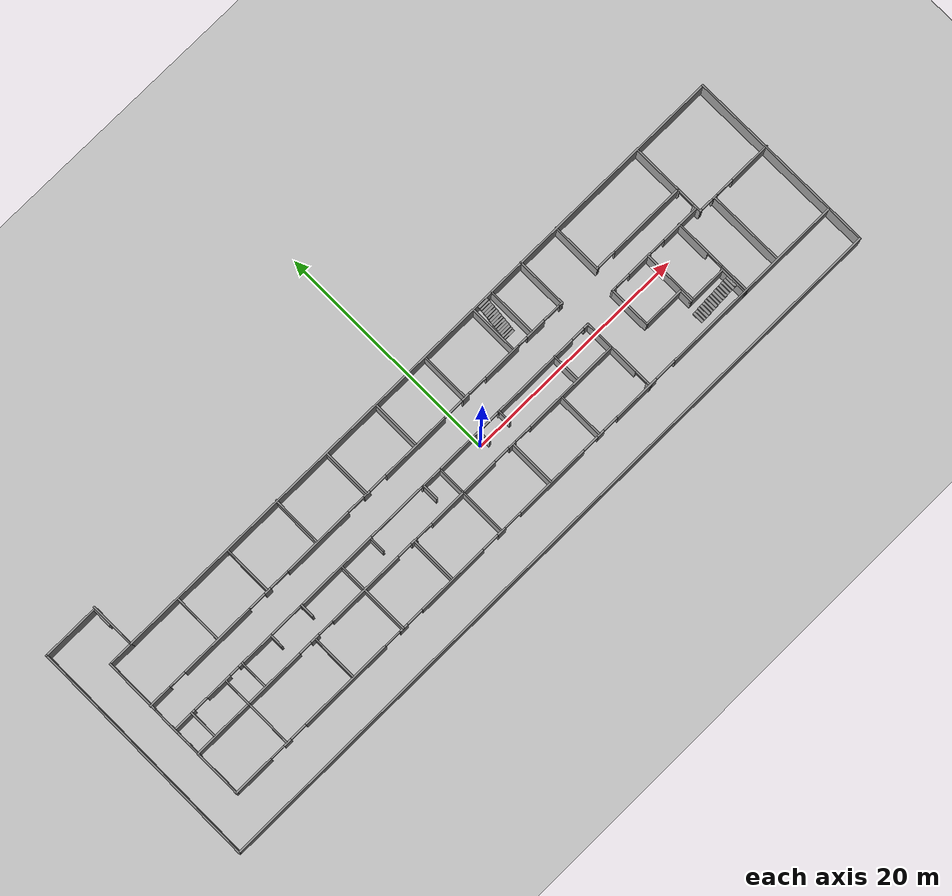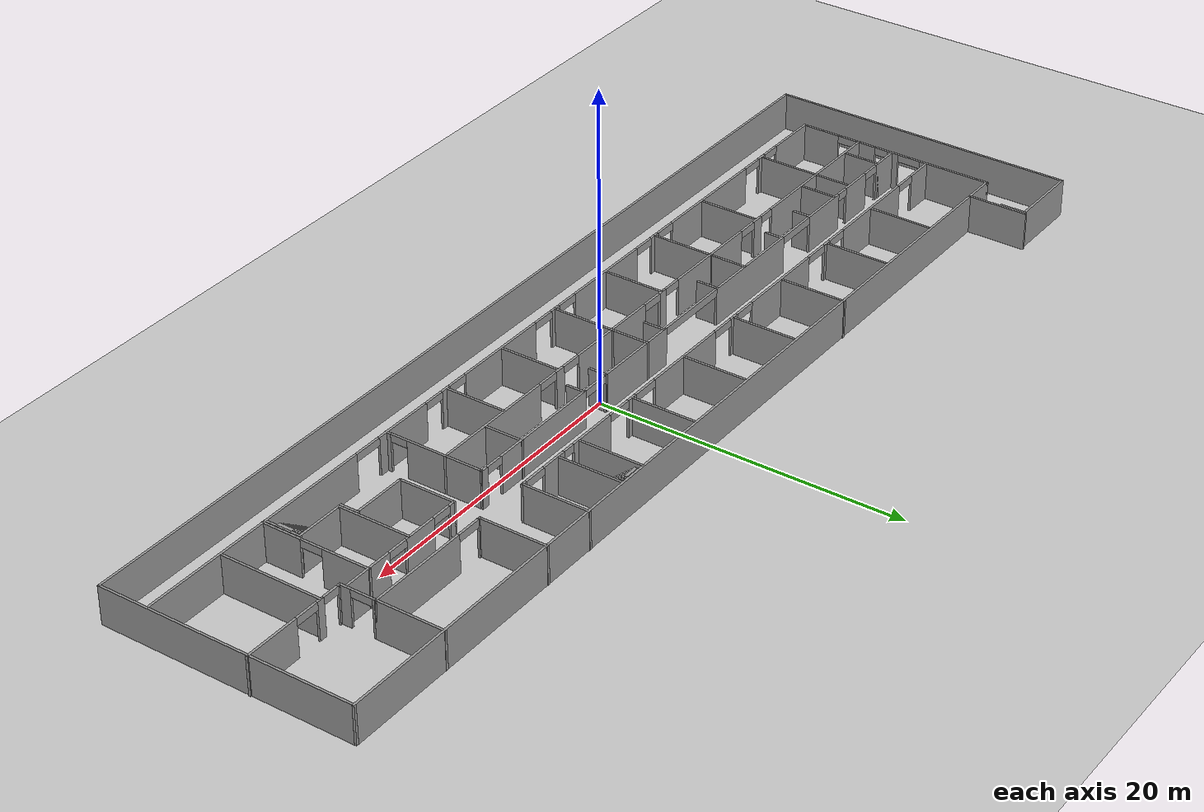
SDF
<sdf version="1.6">
 <world name="default">
  <light name="sun" type="directional">
   <pose>0 0 10 0 -0 0</pose>
   <diffuse>0.8 0.8 0.8 1</diffuse>
   <specular>0.2 0.2 0.2 1</specular>
   <attenuation>
    <range>1000</range>
    <constant>0.9</constant>
    <linear>0.01</linear>
    <quadratic>0.001</quadratic>
   </attenuation>
   <direction>-0.5 0.1 -0.9</direction>
  </light>
  <model name="ground_plane">
   <static>1</static>
   <link name="link">
    <collision name="collision">
     <geometry><plane><normal>0 0 1</normal><size>100 100</size></plane></geometry>
     <surface><friction><ode><mu>100</mu><mu2>50</mu2></ode></friction></surface>
    </collision>
    <visual name="visual">
     <cast_shadows>0</cast_shadows>
     <geometry><plane><normal>0 0 1</normal><size>100 100</size></plane></geometry>
     <material>
      <script><uri>file://media/materials/scripts/gazebo.material</uri><name>Gazebo/Grey</name></script>
     </material>
    </visual>
   </link>
  </model>
  <gravity>0 0 -9.8</gravity>
  <magnetic_field>6e-06 2.3e-05 -4.2e-05</magnetic_field>
  <atmosphere type="adiabatic"/>
  <physics name="default_physics" default="0" type="ode">
   <max_step_size>0.001</max_step_size>
   <real_time_factor>1</real_time_factor>
   <real_time_update_rate>1000</real_time_update_rate>
  </physics>
  <scene><ambient>0.4 0.4 0.4 1</ambient><background>0.7 0.7 0.7 1</background><shadows>1</shadows></scene>
  <audio><device>default</device></audio>
  <spherical_coordinates>
   <surface_model>EARTH_WGS84</surface_model>
   <latitude_deg>0</latitude_deg>
   <longitude_deg>0</longitude_deg>
   <elevation>0</elevation>
   <heading_deg>0</heading_deg>
  </spherical_coordinates>
  <model name="Se1_cut">
   <pose>-1.39677 1.1644 0 0 -0 0</pose>
   <link name="Stairs_0">
    <visual name="Stairs_0_Visual_0">
     <pose>8.95439 3.41699 0.083333 0 -0 -3.14159</pose>
     <geometry><box><size>1 0.196093 0.166667</size></box></geometry>
     <material>
      <script><uri>file://media/materials/scripts/gazebo.material</uri><name>Gazebo/Grey</name></script>
      <ambient>1 1 1 1</ambient>
     </material>
    </visual>
    <collision name="Stairs_0_Collision_0">
     <geometry><box><size>1 0.196093 0.166667</size></box></geometry>
     <pose>8.95439 3.41699 0.083333 0 -0 -3.14159</pose>
    </collision>
    <visual name="Stairs_0_Visual_1">
     <pose>8.95439 3.61308 0.25 0 -0 -3.14159</pose>
     <geometry><box><size>1 0.196093 0.166667</size></box></geometry>
     <material>
      <script><uri>file://media/materials/scripts/gazebo.material</uri><name>Gazebo/Grey</name></script>
      <ambient>1 1 1 1</ambient>
     </material>
    </visual>
    <collision name="Stairs_0_Collision_1">
     <geometry><box><size>1 0.196093 0.166667</size></box></geometry>
     <pose>8.95439 3.61308 0.25 0 -0 -3.14159</pose>
    </collision>
    <visual name="Stairs_0_Visual_2">
     <pose>8.95439 3.80917 0.416667 0 -0 -3.14159</pose>
     <geometry><box><size>1 0.196093 0.166667</size></box></geometry>
     <material>
      <script><uri>file://media/materials/scripts/gazebo.material</uri><name>Gazebo/Grey</name></script>
      <ambient>1 1 1 1</ambient>
     </material>
    </visual>
    <collision name="Stairs_0_Collision_2">
     <geometry><box><size>1 0.196093 0.166667</size></box></geometry>
     <pose>8.95439 3.80917 0.416667 0 -0 -3.14159</pose>
    </collision>
    <visual name="Stairs_0_Visual_3">
     <pose>8.95439 4.00526 0.583333 0 -0 -3.14159</pose>
     <geometry><box><size>1 0.196093 0.166667</size></box></geometry>
     <material>
      <script><uri>file://media/materials/scripts/gazebo.material</uri><name>Gazebo/Grey</name></script>
      <ambient>1 1 1 1</ambient>
     </material>
    </visual>
    <collision name="Stairs_0_Collision_3">
     <geometry><box><size>1 0.196093 0.166667</size></box></geometry>
     <pose>8.95439 4.00526 0.583333 0 -0 -3.14159</pose>
    </collision>
    <visual name="Stairs_0_Visual_4">
     <pose>8.95439 4.20136 0.75 0 -0 -3.14159</pose>
     <geometry><box><size>1 0.196093 0.166667</size></box></geometry>
     <material>
      <script><uri>file://media/materials/scripts/gazebo.material</uri><name>Gazebo/Grey</name></script>
      <ambient>1 1 1 1</ambient>
     </material>
    </visual>
    <collision name="Stairs_0_Collision_4">
     <geometry><box><size>1 0.196093 0.166667</size></box></geometry>
     <pose>8.95439 4.20136 0.75 0 -0 -3.14159</pose>
    </collision>
    <visual name="Stairs_0_Visual_5">
     <pose>8.95439 4.39745 0.916667 0 -0 -3.14159</pose>
     <geometry><box><size>1 0.196093 0.166667</size></box></geometry>
     <material>
      <script><uri>file://media/materials/scripts/gazebo.material</uri><name>Gazebo/Grey</name></script>
      <ambient>1 1 1 1</ambient>
     </material>
    </visual>
    <collision name="Stairs_0_Collision_5">
     <geometry><box><size>1 0.196093 0.166667</size></box></geometry>
     <pose>8.95439 4.39745 0.916667 0 -0 -3.14159</pose>
    </collision>
    <visual name="Stairs_0_Visual_6">
     <pose>8.95439 4.59354 1.08333 0 -0 -3.14159</pose>
     <geometry><box><size>1 0.196093 0.166667</size></box></geometry>
     <material>
      <script><uri>file://media/materials/scripts/gazebo.material</uri><name>Gazebo/Grey</name></script>
      <ambient>1 1 1 1</ambient>
     </material>
    </visual>
    <collision name="Stairs_0_Collision_6">
     <geometry><box><size>1 0.196093 0.166667</size></box></geometry>
     <pose>8.95439 4.59354 1.08333 0 -0 -3.14159</pose>
    </collision>
    <visual name="Stairs_0_Visual_7">
     <pose>8.95439 4.78964 1.25 0 -0 -3.14159</pose>
     <geometry><box><size>1 0.196093 0.166667</size></box></geometry>
     <material>
      <script><uri>file://media/materials/scripts/gazebo.material</uri><name>Gazebo/Grey</name></script>
      <ambient>1 1 1 1</ambient>
     </material>
    </visual>
    <collision name="Stairs_0_Collision_7">
     <geometry><box><size>1 0.196093 0.166667</size></box></geometry>
     <pose>8.95439 4.78964 1.25 0 -0 -3.14159</pose>
    </collision>
    <visual name="Stairs_0_Visual_8">
     <pose>8.95439 4.98573 1.41667 0 -0 -3.14159</pose>
     <geometry><box><size>1 0.196093 0.166667</size></box></geometry>
     <material>
      <script><uri>file://media/materials/scripts/gazebo.material</uri><name>Gazebo/Grey</name></script>
      <ambient>1 1 1 1</ambient>
     </material>
    </visual>
    <collision name="Stairs_0_Collision_8">
     <geometry><box><size>1 0.196093 0.166667</size></box></geometry>
     <pose>8.95439 4.98573 1.41667 0 -0 -3.14159</pose>
    </collision>
    <visual name="Stairs_0_Visual_9">
     <pose>8.95439 5.18182 1.58333 0 -0 -3.14159</pose>
     <geometry><box><size>1 0.196093 0.166667</size></box></geometry>
     <material>
      <script><uri>file://media/materials/scripts/gazebo.material</uri><name>Gazebo/Grey</name></script>
      <ambient>1 1 1 1</ambient>
     </material>
    </visual>
    <collision name="Stairs_0_Collision_9">
     <geometry><box><size>1 0.196093 0.166667</size></box></geometry>
     <pose>8.95439 5.18182 1.58333 0 -0 -3.14159</pose>
    </collision>
    <visual name="Stairs_0_Visual_10">
     <pose>8.95439 5.37792 1.75 0 -0 -3.14159</pose>
     <geometry><box><size>1 0.196093 0.166667</size></box></geometry>
     <material>
      <script><uri>file://media/materials/scripts/gazebo.material</uri><name>Gazebo/Grey</name></script>
      <ambient>1 1 1 1</ambient>
     </material>
    </visual>
    <collision name="Stairs_0_Collision_10">
     <geometry><box><size>1 0.196093 0.166667</size></box></geometry>
     <pose>8.95439 5.37792 1.75 0 -0 -3.14159</pose>
    </collision>
    <visual name="Stairs_0_Visual_11">
     <pose>8.95439 5.57401 1.91667 0 -0 -3.14159</pose>
     <geometry><box><size>1 0.196093 0.166667</size></box></geometry>
     <material>
      <script><uri>file://media/materials/scripts/gazebo.material</uri><name>Gazebo/Grey</name></script>
      <ambient>1 1 1 1</ambient>
     </material>
    </visual>
    <collision name="Stairs_0_Collision_11">
     <geometry><box><size>1 0.196093 0.166667</size></box></geometry>
     <pose>8.95439 5.57401 1.91667 0 -0 -3.14159</pose>
    </collision>
    <visual name="Stairs_0_Visual_12">
     <pose>8.95439 5.7701 2.08333 0 -0 -3.14159</pose>
     <geometry><box><size>1 0.196093 0.166667</size></box></geometry>
     <material>
      <script><uri>file://media/materials/scripts/gazebo.material</uri><name>Gazebo/Grey</name></script>
      <ambient>1 1 1 1</ambient>
     </material>
    </visual>
    <collision name="Stairs_0_Collision_12">
     <geometry><box><size>1 0.196093 0.166667</size></box></geometry>
     <pose>8.95439 5.7701 2.08333 0 -0 -3.14159</pose>
    </collision>
    <visual name="Stairs_0_Visual_13">
     <pose>8.95439 5.9662 2.25 0 -0 -3.14159</pose>
     <geometry><box><size>1 0.196093 0.166667</size></box></geometry>
     <material>
      <script><uri>file://media/materials/scripts/gazebo.material</uri><name>Gazebo/Grey</name></script>
      <ambient>1 1 1 1</ambient>
     </material>
    </visual>
    <collision name="Stairs_0_Collision_13">
     <geometry><box><size>1 0.196093 0.166667</size></box></geometry>
     <pose>8.95439 5.9662 2.25 0 -0 -3.14159</pose>
    </collision>
    <visual name="Stairs_0_Visual_14">
     <pose>8.95439 6.16229 2.41667 0 -0 -3.14159</pose>
     <geometry><box><size>1 0.196093 0.166667</size></box></geometry>
     <material>
      <script><uri>file://media/materials/scripts/gazebo.material</uri><name>Gazebo/Grey</name></script>
      <ambient>1 1 1 1</ambient>
     </material>
    </visual>
    <collision name="Stairs_0_Collision_14">
     <geometry><box><size>1 0.196093 0.166667</size></box></geometry>
     <pose>8.95439 6.16229 2.41667 0 -0 -3.14159</pose>
    </collision>
   </link>
   <link name="Stairs_1">
    <visual name="Stairs_1_Visual_0">
     <pose>20.036 -5.73074 0.083333 0 -0 1.5708</pose>
     <geometry><box><size>1 0.233333 0.166667</size></box></geometry>
     <material>
      <script><uri>file://media/materials/scripts/gazebo.material</uri><name>Gazebo/Grey</name></script>
      <ambient>1 1 1 1</ambient>
     </material>
    </visual>
    <collision name="Stairs_1_Collision_0">
     <geometry><box><size>1 0.233333 0.166667</size></box></geometry>
     <pose>20.036 -5.73074 0.083333 0 -0 1.5708</pose>
    </collision>
    <visual name="Stairs_1_Visual_1">
     <pose>20.2693 -5.73074 0.25 0 -0 1.5708</pose>
     <geometry><box><size>1 0.233333 0.166667</size></box></geometry>
     <material>
      <script><uri>file://media/materials/scripts/gazebo.material</uri><name>Gazebo/Grey</name></script>
      <ambient>1 1 1 1</ambient>
     </material>
    </visual>
    <collision name="Stairs_1_Collision_1">
     <geometry><box><size>1 0.233333 0.166667</size></box></geometry>
     <pose>20.2693 -5.73074 0.25 0 -0 1.5708</pose>
    </collision>
    <visual name="Stairs_1_Visual_2">
     <pose>20.5026 -5.73074 0.416667 0 -0 1.5708</pose>
     <geometry><box><size>1 0.233333 0.166667</size></box></geometry>
     <material>
      <script><uri>file://media/materials/scripts/gazebo.material</uri><name>Gazebo/Grey</name></script>
      <ambient>1 1 1 1</ambient>
     </material>
    </visual>
    <collision name="Stairs_1_Collision_2">
     <geometry><box><size>1 0.233333 0.166667</size></box></geometry>
     <pose>20.5026 -5.73074 0.416667 0 -0 1.5708</pose>
    </collision>
    <visual name="Stairs_1_Visual_3">
     <pose>20.736 -5.73074 0.583333 0 -0 1.5708</pose>
     <geometry><box><size>1 0.233333 0.166667</size></box></geometry>
     <material>
      <script><uri>file://media/materials/scripts/gazebo.material</uri><name>Gazebo/Grey</name></script>
      <ambient>1 1 1 1</ambient>
     </material>
    </visual>
    <collision name="Stairs_1_Collision_3">
     <geometry><box><size>1 0.233333 0.166667</size></box></geometry>
     <pose>20.736 -5.73074 0.583333 0 -0 1.5708</pose>
    </collision>
    <visual name="Stairs_1_Visual_4">
     <pose>20.9693 -5.73074 0.75 0 -0 1.5708</pose>
     <geometry><box><size>1 0.233333 0.166667</size></box></geometry>
     <material>
      <script><uri>file://media/materials/scripts/gazebo.material</uri><name>Gazebo/Grey</name></script>
      <ambient>1 1 1 1</ambient>
     </material>
    </visual>
    <collision name="Stairs_1_Collision_4">
     <geometry><box><size>1 0.233333 0.166667</size></box></geometry>
     <pose>20.9693 -5.73074 0.75 0 -0 1.5708</pose>
    </collision>
    <visual name="Stairs_1_Visual_5">
     <pose>21.2026 -5.73074 0.916667 0 -0 1.5708</pose>
     <geometry><box><size>1 0.233333 0.166667</size></box></geometry>
     <material>
      <script><uri>file://media/materials/scripts/gazebo.material</uri><name>Gazebo/Grey</name></script>
      <ambient>1 1 1 1</ambient>
     </material>
    </visual>
    <collision name="Stairs_1_Collision_5">
     <geometry><box><size>1 0.233333 0.166667</size></box></geometry>
     <pose>21.2026 -5.73074 0.916667 0 -0 1.5708</pose>
    </collision>
    <visual name="Stairs_1_Visual_6">
     <pose>21.436 -5.73074 1.08333 0 -0 1.5708</pose>
     <geometry><box><size>1 0.233333 0.166667</size></box></geometry>
     <material>
      <script><uri>file://media/materials/scripts/gazebo.material</uri><name>Gazebo/Grey</name></script>
      <ambient>1 1 1 1</ambient>
     </material>
    </visual>
    <collision name="Stairs_1_Collision_6">
     <geometry><box><size>1 0.233333 0.166667</size></box></geometry>
     <pose>21.436 -5.73074 1.08333 0 -0 1.5708</pose>
    </collision>
    <visual name="Stairs_1_Visual_7">
     <pose>21.6693 -5.73074 1.25 0 -0 1.5708</pose>
     <geometry><box><size>1 0.233333 0.166667</size></box></geometry>
     <material>
      <script><uri>file://media/materials/scripts/gazebo.material</uri><name>Gazebo/Grey</name></script>
      <ambient>1 1 1 1</ambient>
     </material>
    </visual>
    <collision name="Stairs_1_Collision_7">
     <geometry><box><size>1 0.233333 0.166667</size></box></geometry>
     <pose>21.6693 -5.73074 1.25 0 -0 1.5708</pose>
    </collision>
    <visual name="Stairs_1_Visual_8">
     <pose>21.9026 -5.73074 1.41667 0 -0 1.5708</pose>
     <geometry><box><size>1 0.233333 0.166667</size></box></geometry>
     <material>
      <script><uri>file://media/materials/scripts/gazebo.material</uri><name>Gazebo/Grey</name></script>
      <ambient>1 1 1 1</ambient>
     </material>
    </visual>
    <collision name="Stairs_1_Collision_8">
     <geometry><box><size>1 0.233333 0.166667</size></box></geometry>
     <pose>21.9026 -5.73074 1.41667 0 -0 1.5708</pose>
    </collision>
    <visual name="Stairs_1_Visual_9">
     <pose>22.136 -5.73074 1.58333 0 -0 1.5708</pose>
     <geometry><box><size>1 0.233333 0.166667</size></box></geometry>
     <material>
      <script><uri>file://media/materials/scripts/gazebo.material</uri><name>Gazebo/Grey</name></script>
      <ambient>1 1 1 1</ambient>
     </material>
    </visual>
    <collision name="Stairs_1_Collision_9">
     <geometry><box><size>1 0.233333 0.166667</size></box></geometry>
     <pose>22.136 -5.73074 1.58333 0 -0 1.5708</pose>
    </collision>
    <visual name="Stairs_1_Visual_10">
     <pose>22.3693 -5.73074 1.75 0 -0 1.5708</pose>
     <geometry><box><size>1 0.233333 0.166667</size></box></geometry>
     <material>
      <script><uri>file://media/materials/scripts/gazebo.material</uri><name>Gazebo/Grey</name></script>
      <ambient>1 1 1 1</ambient>
     </material>
    </visual>
    <collision name="Stairs_1_Collision_10">
     <geometry><box><size>1 0.233333 0.166667</size></box></geometry>
     <pose>22.3693 -5.73074 1.75 0 -0 1.5708</pose>
    </collision>
    <visual name="Stairs_1_Visual_11">
     <pose>22.6026 -5.73074 1.91667 0 -0 1.5708</pose>
     <geometry><box><size>1 0.233333 0.166667</size></box></geometry>
     <material>
      <script><uri>file://media/materials/scripts/gazebo.material</uri><name>Gazebo/Grey</name></script>
      <ambient>1 1 1 1</ambient>
     </material>
    </visual>
    <collision name="Stairs_1_Collision_11">
     <geometry><box><size>1 0.233333 0.166667</size></box></geometry>
     <pose>22.6026 -5.73074 1.91667 0 -0 1.5708</pose>
    </collision>
    <visual name="Stairs_1_Visual_12">
     <pose>22.836 -5.73074 2.08333 0 -0 1.5708</pose>
     <geometry><box><size>1 0.233333 0.166667</size></box></geometry>
     <material>
      <script><uri>file://media/materials/scripts/gazebo.material</uri><name>Gazebo/Grey</name></script>
      <ambient>1 1 1 1</ambient>
     </material>
    </visual>
    <collision name="Stairs_1_Collision_12">
     <geometry><box><size>1 0.233333 0.166667</size></box></geometry>
     <pose>22.836 -5.73074 2.08333 0 -0 1.5708</pose>
    </collision>
    <visual name="Stairs_1_Visual_13">
     <pose>23.0693 -5.73074 2.25 0 -0 1.5708</pose>
     <geometry><box><size>1 0.233333 0.166667</size></box></geometry>
     <material>
      <script><uri>file://media/materials/scripts/gazebo.material</uri><name>Gazebo/Grey</name></script>
      <ambient>1 1 1 1</ambient>
     </material>
    </visual>
    <collision name="Stairs_1_Collision_13">
     <geometry><box><size>1 0.233333 0.166667</size></box></geometry>
     <pose>23.0693 -5.73074 2.25 0 -0 1.5708</pose>
    </collision>
    <visual name="Stairs_1_Visual_14">
     <pose>23.3026 -5.73074 2.41667 0 -0 1.5708</pose>
     <geometry><box><size>1 0.233333 0.166667</size></box></geometry>
     <material>
      <script><uri>file://media/materials/scripts/gazebo.material</uri><name>Gazebo/Grey</name></script>
      <ambient>1 1 1 1</ambient>
     </material>
    </visual>
    <collision name="Stairs_1_Collision_14">
     <geometry><box><size>1 0.233333 0.166667</size></box></geometry>
     <pose>23.3026 -5.73074 2.41667 0 -0 1.5708</pose>
    </collision>
   </link>
   <link name="Wall_0">
    <collision name="Wall_0_Collision">
     <geometry><box><size>1.75 0.15 2.5</size></box></geometry>
     <pose>0 0 1.25 0 -0 0</pose>
    </collision>
    <visual name="Wall_0_Visual">
     <pose>0 0 1.25 0 -0 0</pose>
     <geometry><box><size>1.75 0.15 2.5</size></box></geometry>
     <material>
      <script><uri>file://media/materials/scripts/gazebo.material</uri><name>Gazebo/Grey</name></script>
      <ambient>1 1 1 1</ambient>
     </material>
    </visual>
    <pose>-27.7314 9.325 0 0 -0 1.5708</pose>
   </link>
   <link name="Wall_1">
    <collision name="Wall_1_Collision">
     <geometry><box><size>5 0.15 2.5</size></box></geometry>
     <pose>0 0 1.25 0 -0 0</pose>
    </collision>
    <visual name="Wall_1_Visual">
     <pose>0 0 1.25 0 -0 0</pose>
     <geometry><box><size>5 0.15 2.5</size></box></geometry>
     <material>
      <script><uri>file://media/materials/scripts/gazebo.material</uri><name>Gazebo/Grey</name></script>
      <ambient>1 1 1 1</ambient>
     </material>
    </visual>
    <pose>-30.1564 10.125 0 0 -0 3.14159</pose>
   </link>
   <link name="Wall_10">
    <pose>1.36862 -6.975 0 0 -0 0</pose>
    <visual name="Wall_10_Visual_0">
     <pose>-29.3076 0 1.25 0 -0 0</pose>
     <geometry><box><size>3.63484 0.15 2.5</size></box></geometry>
     <material>
      <script><uri>file://media/materials/scripts/gazebo.material</uri><name>Gazebo/Grey</name></script>
      <ambient>1 1 1 1</ambient>
     </material>
    </visual>
    <collision name="Wall_10_Collision_0">
     <geometry><box><size>3.63484 0.15 2.5</size></box></geometry>
     <pose>-29.3076 0 1.25 0 -0 0</pose>
    </collision>
    <visual name="Wall_10_Visual_1">
     <pose>-25.817 0 1.25 0 -0 0</pose>
     <geometry><box><size>0.713595 0.15 2.5</size></box></geometry>
     <material>
      <script><uri>file://media/materials/scripts/gazebo.material</uri><name>Gazebo/Grey</name></script>
      <ambient>1 1 1 1</ambient>
     </material>
    </visual>
    <collision name="Wall_10_Collision_1">
     <geometry><box><size>0.713595 0.15 2.5</size></box></geometry>
     <pose>-25.817 0 1.25 0 -0 0</pose>
    </collision>
    <visual name="Wall_10_Visual_2">
     <pose>-19.8 0 1.25 0 -0 0</pose>
     <geometry><box><size>8.27129 0.15 2.5</size></box></geometry>
     <material>
      <script><uri>file://media/materials/scripts/gazebo.material</uri><name>Gazebo/Grey</name></script>
      <ambient>1 1 1 1</ambient>
     </material>
    </visual>
    <collision name="Wall_10_Collision_2">
     <geometry><box><size>8.27129 0.15 2.5</size></box></geometry>
     <pose>-19.8 0 1.25 0 -0 0</pose>
    </collision>
    <visual name="Wall_10_Visual_3">
     <pose>-13.8092 0 1.25 0 -0 0</pose>
     <geometry><box><size>0.8001 0.15 2.5</size></box></geometry>
     <material>
      <script><uri>file://media/materials/scripts/gazebo.material</uri><name>Gazebo/Grey</name></script>
      <ambient>1 1 1 1</ambient>
     </material>
    </visual>
    <collision name="Wall_10_Collision_3">
     <geometry><box><size>0.8001 0.15 2.5</size></box></geometry>
     <pose>-13.8092 0 1.25 0 -0 0</pose>
    </collision>
    <visual name="Wall_10_Visual_4">
     <pose>-8.68578 0 1.25 0 -0 0</pose>
     <geometry><box><size>6.35145 0.15 2.5</size></box></geometry>
     <material>
      <script><uri>file://media/materials/scripts/gazebo.material</uri><name>Gazebo/Grey</name></script>
      <ambient>1 1 1 1</ambient>
     </material>
    </visual>
    <collision name="Wall_10_Collision_4">
     <geometry><box><size>6.35145 0.15 2.5</size></box></geometry>
     <pose>-8.68578 0 1.25 0 -0 0</pose>
    </collision>
    <visual name="Wall_10_Visual_5">
     <pose>-3.58549 0 1.25 0 -0 0</pose>
     <geometry><box><size>0.8001 0.15 2.5</size></box></geometry>
     <material>
      <script><uri>file://media/materials/scripts/gazebo.material</uri><name>Gazebo/Grey</name></script>
      <ambient>1 1 1 1</ambient>
     </material>
    </visual>
    <collision name="Wall_10_Collision_5">
     <geometry><box><size>0.8001 0.15 2.5</size></box></geometry>
     <pose>-3.58549 0 1.25 0 -0 0</pose>
    </collision>
    <visual name="Wall_10_Visual_6">
     <pose>1.72877 0 1.25 0 -0 0</pose>
     <geometry><box><size>6.64058 0.15 2.5</size></box></geometry>
     <material>
      <script><uri>file://media/materials/scripts/gazebo.material</uri><name>Gazebo/Grey</name></script>
      <ambient>1 1 1 1</ambient>
     </material>
    </visual>
    <collision name="Wall_10_Collision_6">
     <geometry><box><size>6.64058 0.15 2.5</size></box></geometry>
     <pose>1.72877 0 1.25 0 -0 0</pose>
    </collision>
    <visual name="Wall_10_Visual_7">
     <pose>6.82907 0 1.25 0 -0 0</pose>
     <geometry><box><size>0.696012 0.15 2.5</size></box></geometry>
     <material>
      <script><uri>file://media/materials/scripts/gazebo.material</uri><name>Gazebo/Grey</name></script>
      <ambient>1 1 1 1</ambient>
     </material>
    </visual>
    <collision name="Wall_10_Collision_7">
     <geometry><box><size>0.696012 0.15 2.5</size></box></geometry>
     <pose>6.82907 0 1.25 0 -0 0</pose>
    </collision>
    <visual name="Wall_10_Visual_8">
     <pose>10.6539 0 1.25 0 -0 0</pose>
     <geometry><box><size>4.13586 0.15 2.5</size></box></geometry>
     <material>
      <script><uri>file://media/materials/scripts/gazebo.material</uri><name>Gazebo/Grey</name></script>
      <ambient>1 1 1 1</ambient>
     </material>
    </visual>
    <collision name="Wall_10_Collision_8">
     <geometry><box><size>4.13586 0.15 2.5</size></box></geometry>
     <pose>10.6539 0 1.25 0 -0 0</pose>
    </collision>
    <visual name="Wall_10_Visual_9">
     <pose>22.8921 0 1.25 0 -0 0</pose>
     <geometry><box><size>16.4658 0.15 2.5</size></box></geometry>
     <material>
      <script><uri>file://media/materials/scripts/gazebo.material</uri><name>Gazebo/Grey</name></script>
      <ambient>1 1 1 1</ambient>
     </material>
    </visual>
    <collision name="Wall_10_Collision_9">
     <geometry><box><size>16.4658 0.15 2.5</size></box></geometry>
     <pose>22.8921 0 1.25 0 -0 0</pose>
    </collision>
    <visual name="Wall_10_Visual_10">
     <pose>-26.832 0 2.25 0 -0 0</pose>
     <geometry><box><size>1.31635 0.15 0.5</size></box></geometry>
     <material>
      <script><uri>file://media/materials/scripts/gazebo.material</uri><name>Gazebo/Grey</name></script>
      <ambient>1 1 1 1</ambient>
     </material>
    </visual>
    <collision name="Wall_10_Collision_10">
     <geometry><box><size>1.31635 0.15 0.5</size></box></geometry>
     <pose>-26.832 0 2.25 0 -0 0</pose>
    </collision>
    <visual name="Wall_10_Visual_11">
     <pose>-24.6979 0 2.25 0 -0 0</pose>
     <geometry><box><size>1.52453 0.15 0.5</size></box></geometry>
     <material>
      <script><uri>file://media/materials/scripts/gazebo.material</uri><name>Gazebo/Grey</name></script>
      <ambient>1 1 1 1</ambient>
     </material>
    </visual>
    <collision name="Wall_10_Collision_11">
     <geometry><box><size>1.52453 0.15 0.5</size></box></geometry>
     <pose>-24.6979 0 2.25 0 -0 0</pose>
    </collision>
    <visual name="Wall_10_Visual_12">
     <pose>-14.9368 0 2.25 0 -0 0</pose>
     <geometry><box><size>1.45514 0.15 0.5</size></box></geometry>
     <material>
      <script><uri>file://media/materials/scripts/gazebo.material</uri><name>Gazebo/Grey</name></script>
      <ambient>1 1 1 1</ambient>
     </material>
    </visual>
    <collision name="Wall_10_Collision_12">
     <geometry><box><size>1.45514 0.15 0.5</size></box></geometry>
     <pose>-14.9368 0 2.25 0 -0 0</pose>
    </collision>
    <visual name="Wall_10_Visual_13">
     <pose>-12.6353 0 2.25 0 -0 0</pose>
     <geometry><box><size>1.54766 0.15 0.5</size></box></geometry>
     <material>
      <script><uri>file://media/materials/scripts/gazebo.material</uri><name>Gazebo/Grey</name></script>
      <ambient>1 1 1 1</ambient>
     </material>
    </visual>
    <collision name="Wall_10_Collision_13">
     <geometry><box><size>1.54766 0.15 0.5</size></box></geometry>
     <pose>-12.6353 0 2.25 0 -0 0</pose>
    </collision>
    <visual name="Wall_10_Visual_14">
     <pose>-4.7478 0 2.25 0 -0 0</pose>
     <geometry><box><size>1.52453 0.15 0.5</size></box></geometry>
     <material>
      <script><uri>file://media/materials/scripts/gazebo.material</uri><name>Gazebo/Grey</name></script>
      <ambient>1 1 1 1</ambient>
     </material>
    </visual>
    <collision name="Wall_10_Collision_14">
     <geometry><box><size>1.52453 0.15 0.5</size></box></geometry>
     <pose>-4.7478 0 2.25 0 -0 0</pose>
    </collision>
    <visual name="Wall_10_Visual_15">
     <pose>-2.38848 0 2.25 0 -0 0</pose>
     <geometry><box><size>1.59392 0.15 0.5</size></box></geometry>
     <material>
      <script><uri>file://media/materials/scripts/gazebo.material</uri><name>Gazebo/Grey</name></script>
      <ambient>1 1 1 1</ambient>
     </material>
    </visual>
    <collision name="Wall_10_Collision_15">
     <geometry><box><size>1.59392 0.15 0.5</size></box></geometry>
     <pose>-2.38848 0 2.25 0 -0 0</pose>
    </collision>
    <visual name="Wall_10_Visual_16">
     <pose>5.76506 0 2.25 0 -0 0</pose>
     <geometry><box><size>1.432 0.15 0.5</size></box></geometry>
     <material>
      <script><uri>file://media/materials/scripts/gazebo.material</uri><name>Gazebo/Grey</name></script>
      <ambient>1 1 1 1</ambient>
     </material>
    </visual>
    <collision name="Wall_10_Collision_16">
     <geometry><box><size>1.432 0.15 0.5</size></box></geometry>
     <pose>5.76506 0 2.25 0 -0 0</pose>
    </collision>
    <visual name="Wall_10_Visual_17">
     <pose>7.88151 0 2.25 0 -0 0</pose>
     <geometry><box><size>1.40887 0.15 0.5</size></box></geometry>
     <material>
      <script><uri>file://media/materials/scripts/gazebo.material</uri><name>Gazebo/Grey</name></script>
      <ambient>1 1 1 1</ambient>
     </material>
    </visual>
    <collision name="Wall_10_Collision_17">
     <geometry><box><size>1.40887 0.15 0.5</size></box></geometry>
     <pose>7.88151 0 2.25 0 -0 0</pose>
    </collision>
    <visual name="Wall_10_Visual_18">
     <pose>13.6905 0 2.25 0 -0 0</pose>
     <geometry><box><size>1.93741 0.15 0.5</size></box></geometry>
     <material>
      <script><uri>file://media/materials/scripts/gazebo.material</uri><name>Gazebo/Grey</name></script>
      <ambient>1 1 1 1</ambient>
     </material>
    </visual>
    <collision name="Wall_10_Collision_18">
     <geometry><box><size>1.93741 0.15 0.5</size></box></geometry>
     <pose>13.6905 0 2.25 0 -0 0</pose>
    </collision>
   </link>
   <link name="Wall_12">
    <pose>-8.15027 -2.91919 0 0 -0 0</pose>
    <visual name="Wall_12_Visual_0">
     <pose>-16.3333 0 1.25 0 -0 0</pose>
     <geometry><box><size>10.5834 0.15 2.5</size></box></geometry>
     <material>
      <script><uri>file://media/materials/scripts/gazebo.material</uri><name>Gazebo/Grey</name></script>
      <ambient>1 1 1 1</ambient>
     </material>
    </visual>
    <collision name="Wall_12_Collision_0">
     <geometry><box><size>10.5834 0.15 2.5</size></box></geometry>
     <pose>-16.3333 0 1.25 0 -0 0</pose>
    </collision>
    <visual name="Wall_12_Visual_1">
     <pose>-9.48534 0 1.25 0 -0 0</pose>
     <geometry><box><size>0.82277 0.15 2.5</size></box></geometry>
     <material>
      <script><uri>file://media/materials/scripts/gazebo.material</uri><name>Gazebo/Grey</name></script>
      <ambient>1 1 1 1</ambient>
     </material>
    </visual>
    <collision name="Wall_12_Collision_1">
     <geometry><box><size>0.82277 0.15 2.5</size></box></geometry>
     <pose>-9.48534 0 1.25 0 -0 0</pose>
    </collision>
    <visual name="Wall_12_Visual_2">
     <pose>-4.24018 0 1.25 0 -0 0</pose>
     <geometry><box><size>6.85313 0.15 2.5</size></box></geometry>
     <material>
      <script><uri>file://media/materials/scripts/gazebo.material</uri><name>Gazebo/Grey</name></script>
      <ambient>1 1 1 1</ambient>
     </material>
    </visual>
    <collision name="Wall_12_Collision_2">
     <geometry><box><size>6.85313 0.15 2.5</size></box></geometry>
     <pose>-4.24018 0 1.25 0 -0 0</pose>
    </collision>
    <visual name="Wall_12_Visual_3">
     <pose>0.816046 0 1.25 0 -0 0</pose>
     <geometry><box><size>0.62662 0.15 2.5</size></box></geometry>
     <material>
      <script><uri>file://media/materials/scripts/gazebo.material</uri><name>Gazebo/Grey</name></script>
      <ambient>1 1 1 1</ambient>
     </material>
    </visual>
    <collision name="Wall_12_Collision_3">
     <geometry><box><size>0.62662 0.15 2.5</size></box></geometry>
     <pose>0.816046 0 1.25 0 -0 0</pose>
    </collision>
    <visual name="Wall_12_Visual_4">
     <pose>5.98559 0 1.25 0 -0 0</pose>
     <geometry><box><size>6.61716 0.15 2.5</size></box></geometry>
     <material>
      <script><uri>file://media/materials/scripts/gazebo.material</uri><name>Gazebo/Grey</name></script>
      <ambient>1 1 1 1</ambient>
     </material>
    </visual>
    <collision name="Wall_12_Collision_4">
     <geometry><box><size>6.61716 0.15 2.5</size></box></geometry>
     <pose>5.98559 0 1.25 0 -0 0</pose>
    </collision>
    <visual name="Wall_12_Visual_5">
     <pose>11.0915 0 1.25 0 -0 0</pose>
     <geometry><box><size>0.730708 0.15 2.5</size></box></geometry>
     <material>
      <script><uri>file://media/materials/scripts/gazebo.material</uri><name>Gazebo/Grey</name></script>
      <ambient>1 1 1 1</ambient>
     </material>
    </visual>
    <collision name="Wall_12_Collision_5">
     <geometry><box><size>0.730708 0.15 2.5</size></box></geometry>
     <pose>11.0915 0 1.25 0 -0 0</pose>
    </collision>
    <visual name="Wall_12_Visual_6">
     <pose>17.3032 0 1.25 0 -0 0</pose>
     <geometry><box><size>8.64359 0.15 2.5</size></box></geometry>
     <material>
      <script><uri>file://media/materials/scripts/gazebo.material</uri><name>Gazebo/Grey</name></script>
      <ambient>1 1 1 1</ambient>
     </material>
    </visual>
    <collision name="Wall_12_Collision_6">
     <geometry><box><size>8.64359 0.15 2.5</size></box></geometry>
     <pose>17.3032 0 1.25 0 -0 0</pose>
    </collision>
    <visual name="Wall_12_Visual_7">
     <pose>-10.4692 0 2.25 0 -0 0</pose>
     <geometry><box><size>1.14486 0.15 0.5</size></box></geometry>
     <material>
      <script><uri>file://media/materials/scripts/gazebo.material</uri><name>Gazebo/Grey</name></script>
      <ambient>1 1 1 1</ambient>
     </material>
    </visual>
    <collision name="Wall_12_Collision_7">
     <geometry><box><size>1.14486 0.15 0.5</size></box></geometry>
     <pose>-10.4692 0 2.25 0 -0 0</pose>
    </collision>
    <visual name="Wall_12_Visual_8">
     <pose>-8.37035 0 2.25 0 -0 0</pose>
     <geometry><box><size>1.40721 0.15 0.5</size></box></geometry>
     <material>
      <script><uri>file://media/materials/scripts/gazebo.material</uri><name>Gazebo/Grey</name></script>
      <ambient>1 1 1 1</ambient>
     </material>
    </visual>
    <collision name="Wall_12_Collision_8">
     <geometry><box><size>1.40721 0.15 0.5</size></box></geometry>
     <pose>-8.37035 0 2.25 0 -0 0</pose>
    </collision>
    <visual name="Wall_12_Visual_9">
     <pose>-0.155439 0 2.25 0 -0 0</pose>
     <geometry><box><size>1.31635 0.15 0.5</size></box></geometry>
     <material>
      <script><uri>file://media/materials/scripts/gazebo.material</uri><name>Gazebo/Grey</name></script>
      <ambient>1 1 1 1</ambient>
     </material>
    </visual>
    <collision name="Wall_12_Collision_9">
     <geometry><box><size>1.31635 0.15 0.5</size></box></geometry>
     <pose>-0.155439 0 2.25 0 -0 0</pose>
    </collision>
    <visual name="Wall_12_Visual_10">
     <pose>1.90318 0 2.25 0 -0 0</pose>
     <geometry><box><size>1.54766 0.15 0.5</size></box></geometry>
     <material>
      <script><uri>file://media/materials/scripts/gazebo.material</uri><name>Gazebo/Grey</name></script>
      <ambient>1 1 1 1</ambient>
     </material>
    </visual>
    <collision name="Wall_12_Collision_10">
     <geometry><box><size>1.54766 0.15 0.5</size></box></geometry>
     <pose>1.90318 0 2.25 0 -0 0</pose>
    </collision>
    <visual name="Wall_12_Visual_11">
     <pose>10.0102 0 2.25 0 -0 0</pose>
     <geometry><box><size>1.432 0.15 0.5</size></box></geometry>
     <material>
      <script><uri>file://media/materials/scripts/gazebo.material</uri><name>Gazebo/Grey</name></script>
      <ambient>1 1 1 1</ambient>
     </material>
    </visual>
    <collision name="Wall_12_Collision_11">
     <geometry><box><size>1.432 0.15 0.5</size></box></geometry>
     <pose>10.0102 0 2.25 0 -0 0</pose>
    </collision>
    <visual name="Wall_12_Visual_12">
     <pose>12.2191 0 2.25 0 -0 0</pose>
     <geometry><box><size>1.52453 0.15 0.5</size></box></geometry>
     <material>
      <script><uri>file://media/materials/scripts/gazebo.material</uri><name>Gazebo/Grey</name></script>
      <ambient>1 1 1 1</ambient>
     </material>
    </visual>
    <collision name="Wall_12_Collision_12">
     <geometry><box><size>1.52453 0.15 0.5</size></box></geometry>
     <pose>12.2191 0 2.25 0 -0 0</pose>
    </collision>
   </link>
   <link name="Wall_13">
    <pose>13.3997 -4.96918 0 0 0 -1.5708</pose>
    <visual name="Wall_13_Visual_0">
     <pose>-0.786431 0 1.25 0 -0 0</pose>
     <geometry><box><size>2.67714 0.15 2.5</size></box></geometry>
     <material>
      <script><uri>file://media/materials/scripts/gazebo.material</uri><name>Gazebo/Grey</name></script>
      <ambient>1 1 1 1</ambient>
     </material>
    </visual>
    <collision name="Wall_13_Collision_0">
     <geometry><box><size>2.67714 0.15 2.5</size></box></geometry>
     <pose>-0.786431 0 1.25 0 -0 0</pose>
    </collision>
    <visual name="Wall_13_Visual_1">
     <pose>1.90422 0 1.25 0 -0 0</pose>
     <geometry><box><size>0.441555 0.15 2.5</size></box></geometry>
     <material>
      <script><uri>file://media/materials/scripts/gazebo.material</uri><name>Gazebo/Grey</name></script>
      <ambient>1 1 1 1</ambient>
     </material>
    </visual>
    <collision name="Wall_13_Collision_1">
     <geometry><box><size>0.441555 0.15 2.5</size></box></geometry>
     <pose>1.90422 0 1.25 0 -0 0</pose>
    </collision>
    <visual name="Wall_13_Visual_2">
     <pose>1.11779 0 2.25 0 -0 0</pose>
     <geometry><box><size>1.13131 0.15 0.5</size></box></geometry>
     <material>
      <script><uri>file://media/materials/scripts/gazebo.material</uri><name>Gazebo/Grey</name></script>
      <ambient>1 1 1 1</ambient>
     </material>
    </visual>
    <collision name="Wall_13_Collision_2">
     <geometry><box><size>1.13131 0.15 0.5</size></box></geometry>
     <pose>1.11779 0 2.25 0 -0 0</pose>
    </collision>
   </link>
   <link name="Wall_15">
    <pose>-8.15027 -0.45807 0 0 -0 0</pose>
    <visual name="Wall_15_Visual_0">
     <pose>-20.5479 0 1.25 0 -0 0</pose>
     <geometry><box><size>2.15424 0.15 2.5</size></box></geometry>
     <material>
      <script><uri>file://media/materials/scripts/gazebo.material</uri><name>Gazebo/Grey</name></script>
      <ambient>1 1 1 1</ambient>
     </material>
    </visual>
    <collision name="Wall_15_Collision_0">
     <geometry><box><size>2.15424 0.15 2.5</size></box></geometry>
     <pose>-20.5479 0 1.25 0 -0 0</pose>
    </collision>
    <visual name="Wall_15_Visual_1">
     <pose>-17.0143 0 1.25 0 -0 0</pose>
     <geometry><box><size>2.34337 0.15 2.5</size></box></geometry>
     <material>
      <script><uri>file://media/materials/scripts/gazebo.material</uri><name>Gazebo/Grey</name></script>
      <ambient>1 1 1 1</ambient>
     </material>
    </visual>
    <collision name="Wall_15_Collision_1">
     <geometry><box><size>2.34337 0.15 2.5</size></box></geometry>
     <pose>-17.0143 0 1.25 0 -0 0</pose>
    </collision>
    <visual name="Wall_15_Visual_2">
     <pose>-13.2326 0 1.25 0 -0 0</pose>
     <geometry><box><size>3.42005 0.15 2.5</size></box></geometry>
     <material>
      <script><uri>file://media/materials/scripts/gazebo.material</uri><name>Gazebo/Grey</name></script>
      <ambient>1 1 1 1</ambient>
     </material>
    </visual>
    <collision name="Wall_15_Collision_2">
     <geometry><box><size>3.42005 0.15 2.5</size></box></geometry>
     <pose>-13.2326 0 1.25 0 -0 0</pose>
    </collision>
    <visual name="Wall_15_Visual_3">
     <pose>-4.87122 0 1.25 0 -0 0</pose>
     <geometry><box><size>7.37503 0.15 2.5</size></box></geometry>
     <material>
      <script><uri>file://media/materials/scripts/gazebo.material</uri><name>Gazebo/Grey</name></script>
      <ambient>1 1 1 1</ambient>
     </material>
    </visual>
    <collision name="Wall_15_Collision_3">
     <geometry><box><size>7.37503 0.15 2.5</size></box></geometry>
     <pose>-4.87122 0 1.25 0 -0 0</pose>
    </collision>
    <visual name="Wall_15_Visual_4">
     <pose>7.10743 0 1.25 0 -0 0</pose>
     <geometry><box><size>6.08516 0.15 2.5</size></box></geometry>
     <material>
      <script><uri>file://media/materials/scripts/gazebo.material</uri><name>Gazebo/Grey</name></script>
      <ambient>1 1 1 1</ambient>
     </material>
    </visual>
    <collision name="Wall_15_Collision_4">
     <geometry><box><size>6.08516 0.15 2.5</size></box></geometry>
     <pose>7.10743 0 1.25 0 -0 0</pose>
    </collision>
    <visual name="Wall_15_Visual_5">
     <pose>15.9605 0 1.25 0 -0 0</pose>
     <geometry><box><size>7.83181 0.15 2.5</size></box></geometry>
     <material>
      <script><uri>file://media/materials/scripts/gazebo.material</uri><name>Gazebo/Grey</name></script>
      <ambient>1 1 1 1</ambient>
     </material>
    </visual>
    <collision name="Wall_15_Collision_5">
     <geometry><box><size>7.83181 0.15 2.5</size></box></geometry>
     <pose>15.9605 0 1.25 0 -0 0</pose>
    </collision>
    <visual name="Wall_15_Visual_6">
     <pose>21.3626 0 1.25 0 -0 0</pose>
     <geometry><box><size>0.524744 0.15 2.5</size></box></geometry>
     <material>
      <script><uri>file://media/materials/scripts/gazebo.material</uri><name>Gazebo/Grey</name></script>
      <ambient>1 1 1 1</ambient>
     </material>
    </visual>
    <collision name="Wall_15_Collision_6">
     <geometry><box><size>0.524744 0.15 2.5</size></box></geometry>
     <pose>21.3626 0 1.25 0 -0 0</pose>
    </collision>
    <visual name="Wall_15_Visual_7">
     <pose>-18.8284 0 2.25 0 -0 0</pose>
     <geometry><box><size>1.28478 0.15 0.5</size></box></geometry>
     <material>
      <script><uri>file://media/materials/scripts/gazebo.material</uri><name>Gazebo/Grey</name></script>
      <ambient>1 1 1 1</ambient>
     </material>
    </visual>
    <collision name="Wall_15_Collision_7">
     <geometry><box><size>1.28478 0.15 0.5</size></box></geometry>
     <pose>-18.8284 0 2.25 0 -0 0</pose>
    </collision>
    <visual name="Wall_15_Visual_8">
     <pose>-15.3926 0 2.25 0 -0 0</pose>
     <geometry><box><size>0.9 0.15 0.5</size></box></geometry>
     <material>
      <script><uri>file://media/materials/scripts/gazebo.material</uri><name>Gazebo/Grey</name></script>
      <ambient>1 1 1 1</ambient>
     </material>
    </visual>
    <collision name="Wall_15_Collision_8">
     <geometry><box><size>0.9 0.15 0.5</size></box></geometry>
     <pose>-15.3926 0 2.25 0 -0 0</pose>
    </collision>
    <visual name="Wall_15_Visual_9">
     <pose>-10.0406 0 2.25 0 -0 0</pose>
     <geometry><box><size>2.96383 0.15 0.5</size></box></geometry>
     <material>
      <script><uri>file://media/materials/scripts/gazebo.material</uri><name>Gazebo/Grey</name></script>
      <ambient>1 1 1 1</ambient>
     </material>
    </visual>
    <collision name="Wall_15_Collision_9">
     <geometry><box><size>2.96383 0.15 0.5</size></box></geometry>
     <pose>-10.0406 0 2.25 0 -0 0</pose>
    </collision>
    <visual name="Wall_15_Visual_10">
     <pose>1.44057 0 2.25 0 -0 0</pose>
     <geometry><box><size>5.24855 0.15 0.5</size></box></geometry>
     <material>
      <script><uri>file://media/materials/scripts/gazebo.material</uri><name>Gazebo/Grey</name></script>
      <ambient>1 1 1 1</ambient>
     </material>
    </visual>
    <collision name="Wall_15_Collision_10">
     <geometry><box><size>5.24855 0.15 0.5</size></box></geometry>
     <pose>1.44057 0 2.25 0 -0 0</pose>
    </collision>
    <visual name="Wall_15_Visual_11">
     <pose>11.0973 0 2.25 0 -0 0</pose>
     <geometry><box><size>1.89462 0.15 0.5</size></box></geometry>
     <material>
      <script><uri>file://media/materials/scripts/gazebo.material</uri><name>Gazebo/Grey</name></script>
      <ambient>1 1 1 1</ambient>
     </material>
    </visual>
    <collision name="Wall_15_Collision_11">
     <geometry><box><size>1.89462 0.15 0.5</size></box></geometry>
     <pose>11.0973 0 2.25 0 -0 0</pose>
    </collision>
    <visual name="Wall_15_Visual_12">
     <pose>20.4883 0 2.25 0 -0 0</pose>
     <geometry><box><size>1.22383 0.15 0.5</size></box></geometry>
     <material>
      <script><uri>file://media/materials/scripts/gazebo.material</uri><name>Gazebo/Grey</name></script>
      <ambient>1 1 1 1</ambient>
     </material>
    </visual>
    <collision name="Wall_15_Collision_12">
     <geometry><box><size>1.22383 0.15 0.5</size></box></geometry>
     <pose>20.4883 0 2.25 0 -0 0</pose>
    </collision>
   </link>
   <link name="Wall_16">
    <collision name="Wall_16_Collision">
     <geometry><box><size>2.61111 0.15 2.5</size></box></geometry>
     <pose>0 0 1.25 0 -0 0</pose>
    </collision>
    <visual name="Wall_16_Visual">
     <pose>0 0 1.25 0 -0 0</pose>
     <geometry><box><size>2.61111 0.15 2.5</size></box></geometry>
     <material>
      <script><uri>file://media/materials/scripts/gazebo.material</uri><name>Gazebo/Grey</name></script>
      <ambient>1 1 1 1</ambient>
     </material>
    </visual>
    <pose>13.3997 -1.68863 0 0 0 -1.5708</pose>
   </link>
   <link name="Wall_18">
    <collision name="Wall_18_Collision">
     <geometry><box><size>2.5 0.15 2.5</size></box></geometry>
     <pose>0 0 1.25 0 -0 0</pose>
    </collision>
    <visual name="Wall_18_Visual">
     <pose>0 0 1.25 0 -0 0</pose>
     <geometry><box><size>2.5 0.15 2.5</size></box></geometry>
     <material>
      <script><uri>file://media/materials/scripts/gazebo.material</uri><name>Gazebo/Grey</name></script>
      <ambient>1 1 1 1</ambient>
     </material>
    </visual>
    <pose>-27.916 -1.63307 0 0 0 -1.5708</pose>
   </link>
   <link name="Wall_2">
    <collision name="Wall_2_Collision">
     <geometry><box><size>20.5 0.15 2.5</size></box></geometry>
     <pose>0 0 1.25 0 -0 0</pose>
    </collision>
    <visual name="Wall_2_Visual">
     <pose>0 0 1.25 0 -0 0</pose>
     <geometry><box><size>20.5 0.15 2.5</size></box></geometry>
     <material>
      <script><uri>file://media/materials/scripts/gazebo.material</uri><name>Gazebo/Grey</name></script>
      <ambient>1 1 1 1</ambient>
     </material>
    </visual>
    <pose>-32.5814 -0.05 0 0 0 -1.5708</pose>
   </link>
   <link name="Wall_20">
    <collision name="Wall_20_Collision">
     <geometry><box><size>2.57604 0.15 2.5</size></box></geometry>
     <pose>0 0 1.25 0 -0 0</pose>
    </collision>
    <visual name="Wall_20_Visual">
     <pose>0 0 1.25 0 -0 0</pose>
     <geometry><box><size>2.57604 0.15 2.5</size></box></geometry>
     <material>
      <script><uri>file://media/materials/scripts/gazebo.material</uri><name>Gazebo/Grey</name></script>
      <ambient>1 1 1 1</ambient>
     </material>
    </visual>
    <pose>-24.4704 -1.79415 0 0 0 -1.5708</pose>
   </link>
   <link name="Wall_23">
    <collision name="Wall_23_Collision">
     <geometry><box><size>2.5 0.15 2.5</size></box></geometry>
     <pose>0 0 1.25 0 -0 0</pose>
    </collision>
    <visual name="Wall_23_Visual">
     <pose>0 0 1.25 0 -0 0</pose>
     <geometry><box><size>2.5 0.15 2.5</size></box></geometry>
     <material>
      <script><uri>file://media/materials/scripts/gazebo.material</uri><name>Gazebo/Grey</name></script>
      <ambient>1 1 1 1</ambient>
     </material>
    </visual>
    <pose>-22.711 -1.63352 0 0 0 -1.5708</pose>
   </link>
   <link name="Wall_25">
    <collision name="Wall_25_Collision">
     <geometry><box><size>1.25 0.15 2.5</size></box></geometry>
     <pose>0 0 1.25 0 -0 0</pose>
    </collision>
    <visual name="Wall_25_Visual">
     <pose>0 0 1.25 0 -0 0</pose>
     <geometry><box><size>1.25 0.15 2.5</size></box></geometry>
     <material>
      <script><uri>file://media/materials/scripts/gazebo.material</uri><name>Gazebo/Grey</name></script>
      <ambient>1 1 1 1</ambient>
     </material>
    </visual>
    <pose>-19.781 -1.01852 0 0 0 -1.5708</pose>
   </link>
   <link name="Wall_27">
    <collision name="Wall_27_Collision">
     <geometry><box><size>1.25 0.15 2.5</size></box></geometry>
     <pose>0 0 1.25 0 -0 0</pose>
    </collision>
    <visual name="Wall_27_Visual">
     <pose>0 0 1.25 0 -0 0</pose>
     <geometry><box><size>1.25 0.15 2.5</size></box></geometry>
     <material>
      <script><uri>file://media/materials/scripts/gazebo.material</uri><name>Gazebo/Grey</name></script>
      <ambient>1 1 1 1</ambient>
     </material>
    </visual>
    <pose>-16.601 -1.02852 0 0 0 -1.5708</pose>
   </link>
   <link name="Wall_29">
    <collision name="Wall_29_Collision">
     <geometry><box><size>2.5 0.15 2.5</size></box></geometry>
     <pose>0 0 1.25 0 -0 0</pose>
    </collision>
    <visual name="Wall_29_Visual">
     <pose>0 0 1.25 0 -0 0</pose>
     <geometry><box><size>2.5 0.15 2.5</size></box></geometry>
     <material>
      <script><uri>file://media/materials/scripts/gazebo.material</uri><name>Gazebo/Grey</name></script>
      <ambient>1 1 1 1</ambient>
     </material>
    </visual>
    <pose>-12.471 -1.66352 0 0 0 -1.5708</pose>
   </link>
   <link name="Wall_3">
    <collision name="Wall_3_Collision">
     <geometry><box><size>65.25 0.15 2.5</size></box></geometry>
     <pose>0 0 1.25 0 -0 0</pose>
    </collision>
    <visual name="Wall_3_Visual">
     <pose>0 0 1.25 0 -0 0</pose>
     <geometry><box><size>65.25 0.15 2.5</size></box></geometry>
     <material>
      <script><uri>file://media/materials/scripts/gazebo.material</uri><name>Gazebo/Grey</name></script>
      <ambient>1 1 1 1</ambient>
     </material>
    </visual>
    <pose>-0.031375 -10.225 0 0 -0 0</pose>
   </link>
   <link name="Wall_31">
    <collision name="Wall_31_Collision">
     <geometry><box><size>1.5 0.15 2.5</size></box></geometry>
     <pose>0 0 1.25 0 -0 0</pose>
    </collision>
    <visual name="Wall_31_Visual">
     <pose>0 0 1.25 0 -0 0</pose>
     <geometry><box><size>1.5 0.15 2.5</size></box></geometry>
     <material>
      <script><uri>file://media/materials/scripts/gazebo.material</uri><name>Gazebo/Grey</name></script>
      <ambient>1 1 1 1</ambient>
     </material>
    </visual>
    <pose>-9.481 -1.13352 0 0 0 -1.5708</pose>
   </link>
   <link name="Wall_33">
    <collision name="Wall_33_Collision">
     <geometry><box><size>1.5 0.15 2.5</size></box></geometry>
     <pose>0 0 1.25 0 -0 0</pose>
    </collision>
    <visual name="Wall_33_Visual">
     <pose>0 0 1.25 0 -0 0</pose>
     <geometry><box><size>1.5 0.15 2.5</size></box></geometry>
     <material>
      <script><uri>file://media/materials/scripts/gazebo.material</uri><name>Gazebo/Grey</name></script>
      <ambient>1 1 1 1</ambient>
     </material>
    </visual>
    <pose>-3.911 -1.13352 0 0 0 -1.5708</pose>
   </link>
   <link name="Wall_35">
    <collision name="Wall_35_Collision">
     <geometry><box><size>2.5 0.15 2.5</size></box></geometry>
     <pose>0 0 1.25 0 -0 0</pose>
    </collision>
    <visual name="Wall_35_Visual">
     <pose>0 0 1.25 0 -0 0</pose>
     <geometry><box><size>2.5 0.15 2.5</size></box></geometry>
     <material>
      <script><uri>file://media/materials/scripts/gazebo.material</uri><name>Gazebo/Grey</name></script>
      <ambient>1 1 1 1</ambient>
     </material>
    </visual>
    <pose>-2.181 -1.62352 0 0 0 -1.5708</pose>
   </link>
   <link name="Wall_37">
    <collision name="Wall_37_Collision">
     <geometry><box><size>1.25 0.15 2.5</size></box></geometry>
     <pose>0 0 1.25 0 -0 0</pose>
    </collision>
    <visual name="Wall_37_Visual">
     <pose>0 0 1.25 0 -0 0</pose>
     <geometry><box><size>1.25 0.15 2.5</size></box></geometry>
     <material>
      <script><uri>file://media/materials/scripts/gazebo.material</uri><name>Gazebo/Grey</name></script>
      <ambient>1 1 1 1</ambient>
     </material>
    </visual>
    <pose>1.889 -0.998521 0 0 0 -1.5708</pose>
   </link>
   <link name="Wall_39">
    <collision name="Wall_39_Collision">
     <geometry><box><size>1.25 0.15 2.5</size></box></geometry>
     <pose>0 0 1.25 0 -0 0</pose>
    </collision>
    <visual name="Wall_39_Visual">
     <pose>0 0 1.25 0 -0 0</pose>
     <geometry><box><size>1.25 0.15 2.5</size></box></geometry>
     <material>
      <script><uri>file://media/materials/scripts/gazebo.material</uri><name>Gazebo/Grey</name></script>
      <ambient>1 1 1 1</ambient>
     </material>
    </visual>
    <pose>4.019 -1.00852 0 0 0 -1.5708</pose>
   </link>
   <link name="Wall_4">
    <collision name="Wall_4_Collision">
     <geometry><box><size>16.75 0.15 2.5</size></box></geometry>
     <pose>0 0 1.25 0 -0 0</pose>
    </collision>
    <visual name="Wall_4_Visual">
     <pose>0 0 1.25 0 -0 0</pose>
     <geometry><box><size>16.75 0.15 2.5</size></box></geometry>
     <material>
      <script><uri>file://media/materials/scripts/gazebo.material</uri><name>Gazebo/Grey</name></script>
      <ambient>1 1 1 1</ambient>
     </material>
    </visual>
    <pose>32.5186 -1.925 0 0 -0 1.5708</pose>
   </link>
   <link name="Wall_41">
    <collision name="Wall_41_Collision">
     <geometry><box><size>2.5 0.15 2.5</size></box></geometry>
     <pose>0 0 1.25 0 -0 0</pose>
    </collision>
    <visual name="Wall_41_Visual">
     <pose>0 0 1.25 0 -0 0</pose>
     <geometry><box><size>2.5 0.15 2.5</size></box></geometry>
     <material>
      <script><uri>file://media/materials/scripts/gazebo.material</uri><name>Gazebo/Grey</name></script>
      <ambient>1 1 1 1</ambient>
     </material>
    </visual>
    <pose>9.879 -1.60352 0 0 0 -1.5708</pose>
   </link>
   <link name="Wall_46">
    <pose>-8.2779 2.06374 0 0 -0 0</pose>
    <visual name="Wall_46_Visual_0">
     <pose>-20.462 0 1.25 0 -0 0</pose>
     <geometry><box><size>2.07596 0.15 2.5</size></box></geometry>
     <material>
      <script><uri>file://media/materials/scripts/gazebo.material</uri><name>Gazebo/Grey</name></script>
      <ambient>1 1 1 1</ambient>
     </material>
    </visual>
    <collision name="Wall_46_Collision_0">
     <geometry><box><size>2.07596 0.15 2.5</size></box></geometry>
     <pose>-20.462 0 1.25 0 -0 0</pose>
    </collision>
    <visual name="Wall_46_Visual_1">
     <pose>-14.5766 0 1.25 0 -0 0</pose>
     <geometry><box><size>6.67122 0.15 2.5</size></box></geometry>
     <material>
      <script><uri>file://media/materials/scripts/gazebo.material</uri><name>Gazebo/Grey</name></script>
      <ambient>1 1 1 1</ambient>
     </material>
    </visual>
    <collision name="Wall_46_Collision_1">
     <geometry><box><size>6.67122 0.15 2.5</size></box></geometry>
     <pose>-14.5766 0 1.25 0 -0 0</pose>
    </collision>
    <visual name="Wall_46_Visual_2">
     <pose>-9.36125 0 1.25 0 -0 0</pose>
     <geometry><box><size>0.629513 0.15 2.5</size></box></geometry>
     <material>
      <script><uri>file://media/materials/scripts/gazebo.material</uri><name>Gazebo/Grey</name></script>
      <ambient>1 1 1 1</ambient>
     </material>
    </visual>
    <collision name="Wall_46_Collision_2">
     <geometry><box><size>0.629513 0.15 2.5</size></box></geometry>
     <pose>-9.36125 0 1.25 0 -0 0</pose>
    </collision>
    <visual name="Wall_46_Visual_3">
     <pose>-4.12766 0 1.25 0 -0 0</pose>
     <geometry><box><size>6.28205 0.15 2.5</size></box></geometry>
     <material>
      <script><uri>file://media/materials/scripts/gazebo.material</uri><name>Gazebo/Grey</name></script>
      <ambient>1 1 1 1</ambient>
     </material>
    </visual>
    <collision name="Wall_46_Collision_3">
     <geometry><box><size>6.28205 0.15 2.5</size></box></geometry>
     <pose>-4.12766 0 1.25 0 -0 0</pose>
    </collision>
    <visual name="Wall_46_Visual_4">
     <pose>0.926374 0 1.25 0 -0 0</pose>
     <geometry><box><size>0.642812 0.15 2.5</size></box></geometry>
     <material>
      <script><uri>file://media/materials/scripts/gazebo.material</uri><name>Gazebo/Grey</name></script>
      <ambient>1 1 1 1</ambient>
     </material>
    </visual>
    <collision name="Wall_46_Collision_4">
     <geometry><box><size>0.642812 0.15 2.5</size></box></geometry>
     <pose>0.926374 0 1.25 0 -0 0</pose>
    </collision>
    <visual name="Wall_46_Visual_5">
     <pose>5.96711 0 1.25 0 -0 0</pose>
     <geometry><box><size>6.14905 0.15 2.5</size></box></geometry>
     <material>
      <script><uri>file://media/materials/scripts/gazebo.material</uri><name>Gazebo/Grey</name></script>
      <ambient>1 1 1 1</ambient>
     </material>
    </visual>
    <collision name="Wall_46_Collision_5">
     <geometry><box><size>6.14905 0.15 2.5</size></box></geometry>
     <pose>5.96711 0 1.25 0 -0 0</pose>
    </collision>
    <visual name="Wall_46_Visual_6">
     <pose>11.2606 0 1.25 0 -0 0</pose>
     <geometry><box><size>0.722612 0.15 2.5</size></box></geometry>
     <material>
      <script><uri>file://media/materials/scripts/gazebo.material</uri><name>Gazebo/Grey</name></script>
      <ambient>1 1 1 1</ambient>
     </material>
    </visual>
    <collision name="Wall_46_Collision_6">
     <geometry><box><size>0.722612 0.15 2.5</size></box></geometry>
     <pose>11.2606 0 1.25 0 -0 0</pose>
    </collision>
    <visual name="Wall_46_Visual_7">
     <pose>15.1043 0 1.25 0 -0 0</pose>
     <geometry><box><size>3.46243 0.15 2.5</size></box></geometry>
     <material>
      <script><uri>file://media/materials/scripts/gazebo.material</uri><name>Gazebo/Grey</name></script>
      <ambient>1 1 1 1</ambient>
     </material>
    </visual>
    <collision name="Wall_46_Collision_7">
     <geometry><box><size>3.46243 0.15 2.5</size></box></geometry>
     <pose>15.1043 0 1.25 0 -0 0</pose>
    </collision>
    <visual name="Wall_46_Visual_8">
     <pose>18.6421 0 1.25 0 -0 0</pose>
     <geometry><box><size>1.81322 0.15 2.5</size></box></geometry>
     <material>
      <script><uri>file://media/materials/scripts/gazebo.material</uri><name>Gazebo/Grey</name></script>
      <ambient>1 1 1 1</ambient>
     </material>
    </visual>
    <collision name="Wall_46_Collision_8">
     <geometry><box><size>1.81322 0.15 2.5</size></box></geometry>
     <pose>18.6421 0 1.25 0 -0 0</pose>
    </collision>
    <visual name="Wall_46_Visual_9">
     <pose>21.3202 0 1.25 0 -0 0</pose>
     <geometry><box><size>0.359679 0.15 2.5</size></box></geometry>
     <material>
      <script><uri>file://media/materials/scripts/gazebo.material</uri><name>Gazebo/Grey</name></script>
      <ambient>1 1 1 1</ambient>
     </material>
    </visual>
    <collision name="Wall_46_Collision_9">
     <geometry><box><size>0.359679 0.15 2.5</size></box></geometry>
     <pose>21.3202 0 1.25 0 -0 0</pose>
    </collision>
    <visual name="Wall_46_Visual_10">
     <pose>-18.6681 0 2.25 0 -0 0</pose>
     <geometry><box><size>1.51181 0.15 0.5</size></box></geometry>
     <material>
      <script><uri>file://media/materials/scripts/gazebo.material</uri><name>Gazebo/Grey</name></script>
      <ambient>1 1 1 1</ambient>
     </material>
    </visual>
    <collision name="Wall_46_Collision_10">
     <geometry><box><size>1.51181 0.15 0.5</size></box></geometry>
     <pose>-18.6681 0 2.25 0 -0 0</pose>
    </collision>
    <visual name="Wall_46_Visual_11">
     <pose>-10.4585 0 2.25 0 -0 0</pose>
     <geometry><box><size>1.565 0.15 0.5</size></box></geometry>
     <material>
      <script><uri>file://media/materials/scripts/gazebo.material</uri><name>Gazebo/Grey</name></script>
      <ambient>1 1 1 1</ambient>
     </material>
    </visual>
    <collision name="Wall_46_Collision_11">
     <geometry><box><size>1.565 0.15 0.5</size></box></geometry>
     <pose>-10.4585 0 2.25 0 -0 0</pose>
    </collision>
    <visual name="Wall_46_Visual_12">
     <pose>-8.15759 0 2.25 0 -0 0</pose>
     <geometry><box><size>1.77781 0.15 0.5</size></box></geometry>
     <material>
      <script><uri>file://media/materials/scripts/gazebo.material</uri><name>Gazebo/Grey</name></script>
      <ambient>1 1 1 1</ambient>
     </material>
    </visual>
    <collision name="Wall_46_Collision_12">
     <geometry><box><size>1.77781 0.15 0.5</size></box></geometry>
     <pose>-8.15759 0 2.25 0 -0 0</pose>
    </collision>
    <visual name="Wall_46_Visual_13">
     <pose>-0.190835 0 2.25 0 -0 0</pose>
     <geometry><box><size>1.5916 0.15 0.5</size></box></geometry>
     <material>
      <script><uri>file://media/materials/scripts/gazebo.material</uri><name>Gazebo/Grey</name></script>
      <ambient>1 1 1 1</ambient>
     </material>
    </visual>
    <collision name="Wall_46_Collision_13">
     <geometry><box><size>1.5916 0.15 0.5</size></box></geometry>
     <pose>-0.190835 0 2.25 0 -0 0</pose>
    </collision>
    <visual name="Wall_46_Visual_14">
     <pose>2.07018 0 2.25 0 -0 0</pose>
     <geometry><box><size>1.64481 0.15 0.5</size></box></geometry>
     <material>
      <script><uri>file://media/materials/scripts/gazebo.material</uri><name>Gazebo/Grey</name></script>
      <ambient>1 1 1 1</ambient>
     </material>
    </visual>
    <collision name="Wall_46_Collision_14">
     <geometry><box><size>1.64481 0.15 0.5</size></box></geometry>
     <pose>2.07018 0 2.25 0 -0 0</pose>
    </collision>
    <visual name="Wall_46_Visual_15">
     <pose>9.97044 0 2.25 0 -0 0</pose>
     <geometry><box><size>1.85761 0.15 0.5</size></box></geometry>
     <material>
      <script><uri>file://media/materials/scripts/gazebo.material</uri><name>Gazebo/Grey</name></script>
      <ambient>1 1 1 1</ambient>
     </material>
    </visual>
    <collision name="Wall_46_Collision_15">
     <geometry><box><size>1.85761 0.15 0.5</size></box></geometry>
     <pose>9.97044 0 2.25 0 -0 0</pose>
    </collision>
    <visual name="Wall_46_Visual_16">
     <pose>12.4975 0 2.25 0 -0 0</pose>
     <geometry><box><size>1.75121 0.15 0.5</size></box></geometry>
     <material>
      <script><uri>file://media/materials/scripts/gazebo.material</uri><name>Gazebo/Grey</name></script>
      <ambient>1 1 1 1</ambient>
     </material>
    </visual>
    <collision name="Wall_46_Collision_16">
     <geometry><box><size>1.75121 0.15 0.5</size></box></geometry>
     <pose>12.4975 0 2.25 0 -0 0</pose>
    </collision>
    <visual name="Wall_46_Visual_17">
     <pose>17.2855 0 2.25 0 -0 0</pose>
     <geometry><box><size>0.9 0.15 0.5</size></box></geometry>
     <material>
      <script><uri>file://media/materials/scripts/gazebo.material</uri><name>Gazebo/Grey</name></script>
      <ambient>1 1 1 1</ambient>
     </material>
    </visual>
    <collision name="Wall_46_Collision_17">
     <geometry><box><size>0.9 0.15 0.5</size></box></geometry>
     <pose>17.2855 0 2.25 0 -0 0</pose>
    </collision>
    <visual name="Wall_46_Visual_18">
     <pose>20.3445 0 2.25 0 -0 0</pose>
     <geometry><box><size>1.5916 0.15 0.5</size></box></geometry>
     <material>
      <script><uri>file://media/materials/scripts/gazebo.material</uri><name>Gazebo/Grey</name></script>
      <ambient>1 1 1 1</ambient>
     </material>
    </visual>
    <collision name="Wall_46_Collision_18">
     <geometry><box><size>1.5916 0.15 0.5</size></box></geometry>
     <pose>20.3445 0 2.25 0 -0 0</pose>
    </collision>
   </link>
   <link name="Wall_47">
    <collision name="Wall_47_Collision">
     <geometry><box><size>4.5 0.15 2.5</size></box></geometry>
     <pose>0 0 1.25 0 -0 0</pose>
    </collision>
    <visual name="Wall_47_Visual">
     <pose>0 0 1.25 0 -0 0</pose>
     <geometry><box><size>4.5 0.15 2.5</size></box></geometry>
     <material>
      <script><uri>file://media/materials/scripts/gazebo.material</uri><name>Gazebo/Grey</name></script>
      <ambient>1 1 1 1</ambient>
     </material>
    </visual>
    <pose>13.1471 4.23874 0 0 -0 1.5708</pose>
   </link>
   <link name="Wall_49">
    <collision name="Wall_49_Collision">
     <geometry><box><size>4.25 0.15 2.5</size></box></geometry>
     <pose>0 0 1.25 0 -0 0</pose>
    </collision>
    <visual name="Wall_49_Visual">
     <pose>0 0 1.25 0 -0 0</pose>
     <geometry><box><size>4.25 0.15 2.5</size></box></geometry>
     <material>
      <script><uri>file://media/materials/scripts/gazebo.material</uri><name>Gazebo/Grey</name></script>
      <ambient>1 1 1 1</ambient>
     </material>
    </visual>
    <pose>-22.7583 4.23959 0 0 0 -1.5708</pose>
   </link>
   <link name="Wall_5">
    <collision name="Wall_5_Collision">
     <geometry><box><size>60.25 0.15 2.5</size></box></geometry>
     <pose>0 0 1.25 0 -0 0</pose>
    </collision>
    <visual name="Wall_5_Visual">
     <pose>0 0 1.25 0 -0 0</pose>
     <geometry><box><size>60.25 0.15 2.5</size></box></geometry>
     <material>
      <script><uri>file://media/materials/scripts/gazebo.material</uri><name>Gazebo/Grey</name></script>
      <ambient>1 1 1 1</ambient>
     </material>
    </visual>
    <pose>2.46862 6.375 0 0 -0 3.14159</pose>
   </link>
   <link name="Wall_51">
    <collision name="Wall_51_Collision">
     <geometry><box><size>4.25 0.15 2.5</size></box></geometry>
     <pose>0 0 1.25 0 -0 0</pose>
    </collision>
    <visual name="Wall_51_Visual">
     <pose>0 0 1.25 0 -0 0</pose>
     <geometry><box><size>4.25 0.15 2.5</size></box></geometry>
     <material>
      <script><uri>file://media/materials/scripts/gazebo.material</uri><name>Gazebo/Grey</name></script>
      <ambient>1 1 1 1</ambient>
     </material>
    </visual>
    <pose>-17.6222 4.24038 0 0 0 -1.5708</pose>
   </link>
   <link name="Wall_53">
    <collision name="Wall_53_Collision">
     <geometry><box><size>4.5 0.15 2.5</size></box></geometry>
     <pose>0 0 1.25 0 -0 0</pose>
    </collision>
    <visual name="Wall_53_Visual">
     <pose>0 0 1.25 0 -0 0</pose>
     <geometry><box><size>4.5 0.15 2.5</size></box></geometry>
     <material>
      <script><uri>file://media/materials/scripts/gazebo.material</uri><name>Gazebo/Grey</name></script>
      <ambient>1 1 1 1</ambient>
     </material>
    </visual>
    <pose>-12.4852 4.25279 0 0 0 -1.5708</pose>
   </link>
   <link name="Wall_55">
    <collision name="Wall_55_Collision">
     <geometry><box><size>4.25 0.15 2.5</size></box></geometry>
     <pose>0 0 1.25 0 -0 0</pose>
    </collision>
    <visual name="Wall_55_Visual">
     <pose>0 0 1.25 0 -0 0</pose>
     <geometry><box><size>4.25 0.15 2.5</size></box></geometry>
     <material>
      <script><uri>file://media/materials/scripts/gazebo.material</uri><name>Gazebo/Grey</name></script>
      <ambient>1 1 1 1</ambient>
     </material>
    </visual>
    <pose>-7.3248 4.21819 0 0 0 -1.5708</pose>
   </link>
   <link name="Wall_57">
    <collision name="Wall_57_Collision">
     <geometry><box><size>4.25 0.15 2.5</size></box></geometry>
     <pose>0 0 1.25 0 -0 0</pose>
    </collision>
    <visual name="Wall_57_Visual">
     <pose>0 0 1.25 0 -0 0</pose>
     <geometry><box><size>4.25 0.15 2.5</size></box></geometry>
     <material>
      <script><uri>file://media/materials/scripts/gazebo.material</uri><name>Gazebo/Grey</name></script>
      <ambient>1 1 1 1</ambient>
     </material>
    </visual>
    <pose>-2.16437 4.21819 0 0 0 -1.5708</pose>
   </link>
   <link name="Wall_59">
    <collision name="Wall_59_Collision">
     <geometry><box><size>4.25 0.15 2.5</size></box></geometry>
     <pose>0 0 1.25 0 -0 0</pose>
    </collision>
    <visual name="Wall_59_Visual">
     <pose>0 0 1.25 0 -0 0</pose>
     <geometry><box><size>4.25 0.15 2.5</size></box></geometry>
     <material>
      <script><uri>file://media/materials/scripts/gazebo.material</uri><name>Gazebo/Grey</name></script>
      <ambient>1 1 1 1</ambient>
     </material>
    </visual>
    <pose>2.96947 4.24479 0 0 0 -1.5708</pose>
   </link>
   <link name="Wall_6">
    <collision name="Wall_6_Collision">
     <geometry><box><size>4 0.15 2.5</size></box></geometry>
     <pose>0 0 1.25 0 -0 0</pose>
    </collision>
    <visual name="Wall_6_Visual">
     <pose>0 0 1.25 0 -0 0</pose>
     <geometry><box><size>4 0.15 2.5</size></box></geometry>
     <material>
      <script><uri>file://media/materials/scripts/gazebo.material</uri><name>Gazebo/Grey</name></script>
      <ambient>1 1 1 1</ambient>
     </material>
    </visual>
    <pose>-27.5814 8.3 0 0 -0 1.5708</pose>
   </link>
   <link name="Wall_61">
    <collision name="Wall_61_Collision">
     <geometry><box><size>4.25 0.15 2.5</size></box></geometry>
     <pose>0 0 1.25 0 -0 0</pose>
    </collision>
    <visual name="Wall_61_Visual">
     <pose>0 0 1.25 0 -0 0</pose>
     <geometry><box><size>4.25 0.15 2.5</size></box></geometry>
     <material>
      <script><uri>file://media/materials/scripts/gazebo.material</uri><name>Gazebo/Grey</name></script>
      <ambient>1 1 1 1</ambient>
     </material>
    </visual>
    <pose>8.07671 4.24479 0 0 0 -1.5708</pose>
   </link>
   <link name="Wall_63">
    <collision name="Wall_63_Collision">
     <geometry><box><size>4.25 0.15 2.5</size></box></geometry>
     <pose>0 0 1.25 0 -0 0</pose>
    </collision>
    <visual name="Wall_63_Visual">
     <pose>0 0 1.25 0 -0 0</pose>
     <geometry><box><size>4.25 0.15 2.5</size></box></geometry>
     <material>
      <script><uri>file://media/materials/scripts/gazebo.material</uri><name>Gazebo/Grey</name></script>
      <ambient>1 1 1 1</ambient>
     </material>
    </visual>
    <pose>9.99193 4.24479 0 0 0 -1.5708</pose>
   </link>
   <link name="Wall_65">
    <collision name="Wall_65_Collision">
     <geometry><box><size>4.5 0.15 2.5</size></box></geometry>
     <pose>0 0 1.25 0 -0 0</pose>
    </collision>
    <visual name="Wall_65_Visual">
     <pose>0 0 1.25 0 -0 0</pose>
     <geometry><box><size>4.5 0.15 2.5</size></box></geometry>
     <material>
      <script><uri>file://media/materials/scripts/gazebo.material</uri><name>Gazebo/Grey</name></script>
      <ambient>1 1 1 1</ambient>
     </material>
    </visual>
    <pose>16.8814 4.22619 0 0 0 -1.5708</pose>
   </link>
   <link name="Wall_66">
    <pose>21.1814 2.05119 0 0 -0 0</pose>
    <visual name="Wall_66_Visual_0">
     <pose>-4.25666 0 1.25 0 -0 0</pose>
     <geometry><box><size>0.236679 0.15 2.5</size></box></geometry>
     <material>
      <script><uri>file://media/materials/scripts/gazebo.material</uri><name>Gazebo/Grey</name></script>
      <ambient>1 1 1 1</ambient>
     </material>
    </visual>
    <collision name="Wall_66_Collision_0">
     <geometry><box><size>0.236679 0.15 2.5</size></box></geometry>
     <pose>-4.25666 0 1.25 0 -0 0</pose>
    </collision>
    <visual name="Wall_66_Visual_1">
     <pose>0.954042 0 1.25 0 -0 0</pose>
     <geometry><box><size>6.84192 0.15 2.5</size></box></geometry>
     <material>
      <script><uri>file://media/materials/scripts/gazebo.material</uri><name>Gazebo/Grey</name></script>
      <ambient>1 1 1 1</ambient>
     </material>
    </visual>
    <collision name="Wall_66_Collision_1">
     <geometry><box><size>6.84192 0.15 2.5</size></box></geometry>
     <pose>0.954042 0 1.25 0 -0 0</pose>
    </collision>
    <visual name="Wall_66_Visual_2">
     <pose>-3.30262 0 2.25 0 -0 0</pose>
     <geometry><box><size>1.67141 0.15 0.5</size></box></geometry>
     <material>
      <script><uri>file://media/materials/scripts/gazebo.material</uri><name>Gazebo/Grey</name></script>
      <ambient>1 1 1 1</ambient>
     </material>
    </visual>
    <collision name="Wall_66_Collision_2">
     <geometry><box><size>1.67141 0.15 0.5</size></box></geometry>
     <pose>-3.30262 0 2.25 0 -0 0</pose>
    </collision>
   </link>
   <link name="Wall_67">
    <collision name="Wall_67_Collision">
     <geometry><box><size>4.5 0.15 2.5</size></box></geometry>
     <pose>0 0 1.25 0 -0 0</pose>
    </collision>
    <visual name="Wall_67_Visual">
     <pose>0 0 1.25 0 -0 0</pose>
     <geometry><box><size>4.5 0.15 2.5</size></box></geometry>
     <material>
      <script><uri>file://media/materials/scripts/gazebo.material</uri><name>Gazebo/Grey</name></script>
      <ambient>1 1 1 1</ambient>
     </material>
    </visual>
    <pose>25.4814 4.22619 0 0 -0 1.5708</pose>
   </link>
   <link name="Wall_69">
    <pose>25.4814 0.876187 0 0 0 -1.5708</pose>
    <visual name="Wall_69_Visual_0">
     <pose>-1.11105 0 1.25 0 -0 0</pose>
     <geometry><box><size>0.278249 0.15 2.5</size></box></geometry>
     <material>
      <script><uri>file://media/materials/scripts/gazebo.material</uri><name>Gazebo/Grey</name></script>
      <ambient>1 1 1 1</ambient>
     </material>
    </visual>
    <collision name="Wall_69_Collision_0">
     <geometry><box><size>0.278249 0.15 2.5</size></box></geometry>
     <pose>-1.11105 0 1.25 0 -0 0</pose>
    </collision>
    <visual name="Wall_69_Visual_1">
     <pose>0.855126 0 1.25 0 -0 0</pose>
     <geometry><box><size>0.790095 0.15 2.5</size></box></geometry>
     <material>
      <script><uri>file://media/materials/scripts/gazebo.material</uri><name>Gazebo/Grey</name></script>
      <ambient>1 1 1 1</ambient>
     </material>
    </visual>
    <collision name="Wall_69_Collision_1">
     <geometry><box><size>0.790095 0.15 2.5</size></box></geometry>
     <pose>0.855126 0 1.25 0 -0 0</pose>
    </collision>
    <visual name="Wall_69_Visual_2">
     <pose>-0.255923 0 2.25 0 -0 0</pose>
     <geometry><box><size>1.432 0.15 0.5</size></box></geometry>
     <material>
      <script><uri>file://media/materials/scripts/gazebo.material</uri><name>Gazebo/Grey</name></script>
      <ambient>1 1 1 1</ambient>
     </material>
    </visual>
    <collision name="Wall_69_Collision_2">
     <geometry><box><size>1.432 0.15 0.5</size></box></geometry>
     <pose>-0.255923 0 2.25 0 -0 0</pose>
    </collision>
   </link>
   <link name="Wall_70">
    <pose>29.0314 -0.298813 0 0 -0 0</pose>
    <visual name="Wall_70_Visual_0">
     <pose>-3.49078 0 1.25 0 -0 0</pose>
     <geometry><box><size>0.268443 0.15 2.5</size></box></geometry>
     <material>
      <script><uri>file://media/materials/scripts/gazebo.material</uri><name>Gazebo/Grey</name></script>
      <ambient>1 1 1 1</ambient>
     </material>
    </visual>
    <collision name="Wall_70_Collision_0">
     <geometry><box><size>0.268443 0.15 2.5</size></box></geometry>
     <pose>-3.49078 0 1.25 0 -0 0</pose>
    </collision>
    <visual name="Wall_70_Visual_1">
     <pose>-1.9689 0 1.25 0 -0 0</pose>
     <geometry><box><size>0.496511 0.15 2.5</size></box></geometry>
     <material>
      <script><uri>file://media/materials/scripts/gazebo.material</uri><name>Gazebo/Grey</name></script>
      <ambient>1 1 1 1</ambient>
     </material>
    </visual>
    <collision name="Wall_70_Collision_1">
     <geometry><box><size>0.496511 0.15 2.5</size></box></geometry>
     <pose>-1.9689 0 1.25 0 -0 0</pose>
    </collision>
    <visual name="Wall_70_Visual_2">
     <pose>1.76128 0 1.25 0 -0 0</pose>
     <geometry><box><size>3.72744 0.15 2.5</size></box></geometry>
     <material>
      <script><uri>file://media/materials/scripts/gazebo.material</uri><name>Gazebo/Grey</name></script>
      <ambient>1 1 1 1</ambient>
     </material>
    </visual>
    <collision name="Wall_70_Collision_2">
     <geometry><box><size>3.72744 0.15 2.5</size></box></geometry>
     <pose>1.76128 0 1.25 0 -0 0</pose>
    </collision>
    <visual name="Wall_70_Visual_3">
     <pose>-2.78686 0 2.25 0 -0 0</pose>
     <geometry><box><size>1.1394 0.15 0.5</size></box></geometry>
     <material>
      <script><uri>file://media/materials/scripts/gazebo.material</uri><name>Gazebo/Grey</name></script>
      <ambient>1 1 1 1</ambient>
     </material>
    </visual>
    <collision name="Wall_70_Collision_3">
     <geometry><box><size>1.1394 0.15 0.5</size></box></geometry>
     <pose>-2.78686 0 2.25 0 -0 0</pose>
    </collision>
    <visual name="Wall_70_Visual_4">
     <pose>-0.911541 0 2.25 0 -0 0</pose>
     <geometry><box><size>1.6182 0.15 0.5</size></box></geometry>
     <material>
      <script><uri>file://media/materials/scripts/gazebo.material</uri><name>Gazebo/Grey</name></script>
      <ambient>1 1 1 1</ambient>
     </material>
    </visual>
    <collision name="Wall_70_Collision_4">
     <geometry><box><size>1.6182 0.15 0.5</size></box></geometry>
     <pose>-0.911541 0 2.25 0 -0 0</pose>
    </collision>
   </link>
   <link name="Wall_72">
    <collision name="Wall_72_Collision">
     <geometry><box><size>3.75 0.15 2.5</size></box></geometry>
     <pose>0 0 1.25 0 -0 0</pose>
    </collision>
    <visual name="Wall_72_Visual">
     <pose>0 0 1.25 0 -0 0</pose>
     <geometry><box><size>3.75 0.15 2.5</size></box></geometry>
     <material>
      <script><uri>file://media/materials/scripts/gazebo.material</uri><name>Gazebo/Grey</name></script>
      <ambient>1 1 1 1</ambient>
     </material>
    </visual>
    <pose>16.5155 -1.74337 0 0 0 -1.5708</pose>
   </link>
   <link name="Wall_73">
    <collision name="Wall_73_Collision">
     <geometry><box><size>3.75 0.15 2.5</size></box></geometry>
     <pose>0 0 1.25 0 -0 0</pose>
    </collision>
    <visual name="Wall_73_Visual">
     <pose>0 0 1.25 0 -0 0</pose>
     <geometry><box><size>3.75 0.15 2.5</size></box></geometry>
     <material>
      <script><uri>file://media/materials/scripts/gazebo.material</uri><name>Gazebo/Grey</name></script>
      <ambient>1 1 1 1</ambient>
     </material>
    </visual>
    <pose>18.3155 -3.54337 0 0 -0 0</pose>
   </link>
   <link name="Wall_74">
    <collision name="Wall_74_Collision">
     <geometry><box><size>1.25 0.15 2.5</size></box></geometry>
     <pose>0 0 1.25 0 -0 0</pose>
    </collision>
    <visual name="Wall_74_Visual">
     <pose>0 0 1.25 0 -0 0</pose>
     <geometry><box><size>1.25 0.15 2.5</size></box></geometry>
     <material>
      <script><uri>file://media/materials/scripts/gazebo.material</uri><name>Gazebo/Grey</name></script>
      <ambient>1 1 1 1</ambient>
     </material>
    </visual>
    <pose>20.1155 -4.09337 0 0 0 -1.5708</pose>
   </link>
   <link name="Wall_75">
    <collision name="Wall_75_Collision">
     <geometry><box><size>3.5 0.15 2.5</size></box></geometry>
     <pose>0 0 1.25 0 -0 0</pose>
    </collision>
    <visual name="Wall_75_Visual">
     <pose>0 0 1.25 0 -0 0</pose>
     <geometry><box><size>3.5 0.15 2.5</size></box></geometry>
     <material>
      <script><uri>file://media/materials/scripts/gazebo.material</uri><name>Gazebo/Grey</name></script>
      <ambient>1 1 1 1</ambient>
     </material>
    </visual>
    <pose>21.7905 -4.64337 0 0 -0 0</pose>
   </link>
   <link name="Wall_77">
    <collision name="Wall_77_Collision">
     <geometry><box><size>2.5 0.15 2.5</size></box></geometry>
     <pose>0 0 1.25 0 -0 0</pose>
    </collision>
    <visual name="Wall_77_Visual">
     <pose>0 0 1.25 0 -0 0</pose>
     <geometry><box><size>2.5 0.15 2.5</size></box></geometry>
     <material>
      <script><uri>file://media/materials/scripts/gazebo.material</uri><name>Gazebo/Grey</name></script>
      <ambient>1 1 1 1</ambient>
     </material>
    </visual>
    <pose>23.4655 -5.81837 0 0 0 -1.5708</pose>
   </link>
   <link name="Wall_79">
    <pose>20.9405 0.056629 0 0 -0 0</pose>
    <visual name="Wall_79_Visual_0">
     <pose>-4.25855 0 1.25 0 -0 0</pose>
     <geometry><box><size>0.482903 0.15 2.5</size></box></geometry>
     <material>
      <script><uri>file://media/materials/scripts/gazebo.material</uri><name>Gazebo/Grey</name></script>
      <ambient>1 1 1 1</ambient>
     </material>
    </visual>
    <collision name="Wall_79_Collision_0">
     <geometry><box><size>0.482903 0.15 2.5</size></box></geometry>
     <pose>-4.25855 0 1.25 0 -0 0</pose>
    </collision>
    <visual name="Wall_79_Visual_1">
     <pose>-1.51223 0 1.25 0 -0 0</pose>
     <geometry><box><size>2.30532 0.15 2.5</size></box></geometry>
     <material>
      <script><uri>file://media/materials/scripts/gazebo.material</uri><name>Gazebo/Grey</name></script>
      <ambient>1 1 1 1</ambient>
     </material>
    </visual>
    <collision name="Wall_79_Collision_1">
     <geometry><box><size>2.30532 0.15 2.5</size></box></geometry>
     <pose>-1.51223 0 1.25 0 -0 0</pose>
    </collision>
    <visual name="Wall_79_Visual_2">
     <pose>2.77292 0 1.25 0 -0 0</pose>
     <geometry><box><size>3.45417 0.15 2.5</size></box></geometry>
     <material>
      <script><uri>file://media/materials/scripts/gazebo.material</uri><name>Gazebo/Grey</name></script>
      <ambient>1 1 1 1</ambient>
     </material>
    </visual>
    <collision name="Wall_79_Collision_2">
     <geometry><box><size>3.45417 0.15 2.5</size></box></geometry>
     <pose>2.77292 0 1.25 0 -0 0</pose>
    </collision>
    <visual name="Wall_79_Visual_3">
     <pose>-3.341 0 2.25 0 -0 0</pose>
     <geometry><box><size>1.3522 0.15 0.5</size></box></geometry>
     <material>
      <script><uri>file://media/materials/scripts/gazebo.material</uri><name>Gazebo/Grey</name></script>
      <ambient>1 1 1 1</ambient>
     </material>
    </visual>
    <collision name="Wall_79_Collision_3">
     <geometry><box><size>1.3522 0.15 0.5</size></box></geometry>
     <pose>-3.341 0 2.25 0 -0 0</pose>
    </collision>
    <visual name="Wall_79_Visual_4">
     <pose>0.343132 0 2.25 0 -0 0</pose>
     <geometry><box><size>1.4054 0.15 0.5</size></box></geometry>
     <material>
      <script><uri>file://media/materials/scripts/gazebo.material</uri><name>Gazebo/Grey</name></script>
      <ambient>1 1 1 1</ambient>
     </material>
    </visual>
    <collision name="Wall_79_Collision_4">
     <geometry><box><size>1.4054 0.15 0.5</size></box></geometry>
     <pose>0.343132 0 2.25 0 -0 0</pose>
    </collision>
   </link>
   <link name="Wall_8">
    <collision name="Wall_8_Collision">
     <geometry><box><size>2.25 0.15 2.5</size></box></geometry>
     <pose>0 0 1.25 0 -0 0</pose>
    </collision>
    <visual name="Wall_8_Visual">
     <pose>0 0 1.25 0 -0 0</pose>
     <geometry><box><size>2.25 0.15 2.5</size></box></geometry>
     <material>
      <script><uri>file://media/materials/scripts/gazebo.material</uri><name>Gazebo/Grey</name></script>
      <ambient>1 1 1 1</ambient>
     </material>
    </visual>
    <pose>-28.6314 6.375 0 0 -0 3.14159</pose>
   </link>
   <link name="Wall_81">
    <collision name="Wall_81_Collision">
     <geometry><box><size>4.75 0.15 2.5</size></box></geometry>
     <pose>0 0 1.25 0 -0 0</pose>
    </collision>
    <visual name="Wall_81_Visual">
     <pose>0 0 1.25 0 -0 0</pose>
     <geometry><box><size>4.75 0.15 2.5</size></box></geometry>
     <material>
      <script><uri>file://media/materials/scripts/gazebo.material</uri><name>Gazebo/Grey</name></script>
      <ambient>1 1 1 1</ambient>
     </material>
    </visual>
    <pose>20.2773 -2.2622 0 0 0 -1.5708</pose>
   </link>
   <link name="Wall_83">
    <pose>23.6544 -3.44281 0 0 0 -1.5708</pose>
    <visual name="Wall_83_Visual_0">
     <pose>-2.05064 0 1.25 0 -0 0</pose>
     <geometry><box><size>3.14871 0.15 2.5</size></box></geometry>
     <material>
      <script><uri>file://media/materials/scripts/gazebo.material</uri><name>Gazebo/Grey</name></script>
      <ambient>1 1 1 1</ambient>
     </material>
    </visual>
    <collision name="Wall_83_Collision_0">
     <geometry><box><size>3.14871 0.15 2.5</size></box></geometry>
     <pose>-2.05064 0 1.25 0 -0 0</pose>
    </collision>
    <visual name="Wall_83_Visual_1">
     <pose>2.30366 0 1.25 0 -0 0</pose>
     <geometry><box><size>2.64268 0.15 2.5</size></box></geometry>
     <material>
      <script><uri>file://media/materials/scripts/gazebo.material</uri><name>Gazebo/Grey</name></script>
      <ambient>1 1 1 1</ambient>
     </material>
    </visual>
    <collision name="Wall_83_Collision_1">
     <geometry><box><size>2.64268 0.15 2.5</size></box></geometry>
     <pose>2.30366 0 1.25 0 -0 0</pose>
    </collision>
    <visual name="Wall_83_Visual_2">
     <pose>0.253014 0 2.25 0 -0 0</pose>
     <geometry><box><size>1.4586 0.15 0.5</size></box></geometry>
     <material>
      <script><uri>file://media/materials/scripts/gazebo.material</uri><name>Gazebo/Grey</name></script>
      <ambient>1 1 1 1</ambient>
     </material>
    </visual>
    <collision name="Wall_83_Collision_2">
     <geometry><box><size>1.4586 0.15 0.5</size></box></geometry>
     <pose>0.253014 0 2.25 0 -0 0</pose>
    </collision>
   </link>
   <link name="Wall_85">
    <collision name="Wall_85_Collision">
     <geometry><box><size>6.75 0.15 2.5</size></box></geometry>
     <pose>0 0 1.25 0 -0 0</pose>
    </collision>
    <visual name="Wall_85_Visual">
     <pose>0 0 1.25 0 -0 0</pose>
     <geometry><box><size>6.75 0.15 2.5</size></box></geometry>
     <material>
      <script><uri>file://media/materials/scripts/gazebo.material</uri><name>Gazebo/Grey</name></script>
      <ambient>1 1 1 1</ambient>
     </material>
    </visual>
    <pose>27.0083 -3.60916 0 0 0 -1.5708</pose>
   </link>
   <link name="Wall_87">
    <collision name="Wall_87_Collision">
     <geometry><box><size>4 0.15 2.5</size></box></geometry>
     <pose>0 0 1.25 0 -0 0</pose>
    </collision>
    <visual name="Wall_87_Visual">
     <pose>0 0 1.25 0 -0 0</pose>
     <geometry><box><size>4 0.15 2.5</size></box></geometry>
     <material>
      <script><uri>file://media/materials/scripts/gazebo.material</uri><name>Gazebo/Grey</name></script>
      <ambient>1 1 1 1</ambient>
     </material>
    </visual>
    <pose>-24.4704 -4.93217 0 0 0 -1.5708</pose>
   </link>
   <link name="Wall_89">
    <collision name="Wall_89_Collision">
     <geometry><box><size>4 0.15 2.5</size></box></geometry>
     <pose>0 0 1.25 0 -0 0</pose>
    </collision>
    <visual name="Wall_89_Visual">
     <pose>0 0 1.25 0 -0 0</pose>
     <geometry><box><size>4 0.15 2.5</size></box></geometry>
     <material>
      <script><uri>file://media/materials/scripts/gazebo.material</uri><name>Gazebo/Grey</name></script>
      <ambient>1 1 1 1</ambient>
     </material>
    </visual>
    <pose>-17.6091 -4.94228 0 0 0 -1.5708</pose>
   </link>
   <link name="Wall_9">
    <pose>-29.6814 -0.3 0 0 0 -1.5708</pose>
    <visual name="Wall_9_Visual_0">
     <pose>-4.31652 0 1.25 0 -0 0</pose>
     <geometry><box><size>4.86697 0.15 2.5</size></box></geometry>
     <material>
      <script><uri>file://media/materials/scripts/gazebo.material</uri><name>Gazebo/Grey</name></script>
      <ambient>1 1 1 1</ambient>
     </material>
    </visual>
    <collision name="Wall_9_Collision_0">
     <geometry><box><size>4.86697 0.15 2.5</size></box></geometry>
     <pose>-4.31652 0 1.25 0 -0 0</pose>
    </collision>
    <visual name="Wall_9_Visual_1">
     <pose>0.092822 0 1.25 0 -0 0</pose>
     <geometry><box><size>0.80276 0.15 2.5</size></box></geometry>
     <material>
      <script><uri>file://media/materials/scripts/gazebo.material</uri><name>Gazebo/Grey</name></script>
      <ambient>1 1 1 1</ambient>
     </material>
    </visual>
    <collision name="Wall_9_Collision_1">
     <geometry><box><size>0.80276 0.15 2.5</size></box></geometry>
     <pose>0.092822 0 1.25 0 -0 0</pose>
    </collision>
    <visual name="Wall_9_Visual_2">
     <pose>2.10756 0 1.25 0 -0 0</pose>
     <geometry><box><size>1.42671 0.15 2.5</size></box></geometry>
     <material>
      <script><uri>file://media/materials/scripts/gazebo.material</uri><name>Gazebo/Grey</name></script>
      <ambient>1 1 1 1</ambient>
     </material>
    </visual>
    <collision name="Wall_9_Collision_2">
     <geometry><box><size>1.42671 0.15 2.5</size></box></geometry>
     <pose>2.10756 0 1.25 0 -0 0</pose>
    </collision>
    <visual name="Wall_9_Visual_3">
     <pose>5.43207 0 1.25 0 -0 0</pose>
     <geometry><box><size>2.63587 0.15 2.5</size></box></geometry>
     <material>
      <script><uri>file://media/materials/scripts/gazebo.material</uri><name>Gazebo/Grey</name></script>
      <ambient>1 1 1 1</ambient>
     </material>
    </visual>
    <collision name="Wall_9_Collision_3">
     <geometry><box><size>2.63587 0.15 2.5</size></box></geometry>
     <pose>5.43207 0 1.25 0 -0 0</pose>
    </collision>
    <visual name="Wall_9_Visual_4">
     <pose>-1.0958 0 2.25 0 -0 0</pose>
     <geometry><box><size>1.57448 0.15 0.5</size></box></geometry>
     <material>
      <script><uri>file://media/materials/scripts/gazebo.material</uri><name>Gazebo/Grey</name></script>
      <ambient>1 1 1 1</ambient>
     </material>
    </visual>
    <collision name="Wall_9_Collision_4">
     <geometry><box><size>1.57448 0.15 0.5</size></box></geometry>
     <pose>-1.0958 0 2.25 0 -0 0</pose>
    </collision>
    <visual name="Wall_9_Visual_5">
     <pose>0.944202 0 2.25 0 -0 0</pose>
     <geometry><box><size>0.9 0.15 0.5</size></box></geometry>
     <material>
      <script><uri>file://media/materials/scripts/gazebo.material</uri><name>Gazebo/Grey</name></script>
      <ambient>1 1 1 1</ambient>
     </material>
    </visual>
    <collision name="Wall_9_Collision_5">
     <geometry><box><size>0.9 0.15 0.5</size></box></geometry>
     <pose>0.944202 0 2.25 0 -0 0</pose>
    </collision>
    <visual name="Wall_9_Visual_6">
     <pose>3.46752 0 2.25 0 -0 0</pose>
     <geometry><box><size>1.29322 0.15 0.5</size></box></geometry>
     <material>
      <script><uri>file://media/materials/scripts/gazebo.material</uri><name>Gazebo/Grey</name></script>
      <ambient>1 1 1 1</ambient>
     </material>
    </visual>
    <collision name="Wall_9_Collision_6">
     <geometry><box><size>1.29322 0.15 0.5</size></box></geometry>
     <pose>3.46752 0 2.25 0 -0 0</pose>
    </collision>
   </link>
   <link name="Wall_91">
    <collision name="Wall_91_Collision">
     <geometry><box><size>4.25 0.15 2.5</size></box></geometry>
     <pose>0 0 1.25 0 -0 0</pose>
    </collision>
    <visual name="Wall_91_Visual">
     <pose>0 0 1.25 0 -0 0</pose>
     <geometry><box><size>4.25 0.15 2.5</size></box></geometry>
     <material>
      <script><uri>file://media/materials/scripts/gazebo.material</uri><name>Gazebo/Grey</name></script>
      <ambient>1 1 1 1</ambient>
     </material>
    </visual>
    <pose>-12.471 -4.88852 0 0 0 -1.5708</pose>
   </link>
   <link name="Wall_93">
    <collision name="Wall_93_Collision">
     <geometry><box><size>4 0.15 2.5</size></box></geometry>
     <pose>0 0 1.25 0 -0 0</pose>
    </collision>
    <visual name="Wall_93_Visual">
     <pose>0 0 1.25 0 -0 0</pose>
     <geometry><box><size>4 0.15 2.5</size></box></geometry>
     <material>
      <script><uri>file://media/materials/scripts/gazebo.material</uri><name>Gazebo/Grey</name></script>
      <ambient>1 1 1 1</ambient>
     </material>
    </visual>
    <pose>-7.29761 -4.91186 0 0 0 -1.5708</pose>
   </link>
   <link name="Wall_95">
    <collision name="Wall_95_Collision">
     <geometry><box><size>4.25 0.15 2.5</size></box></geometry>
     <pose>0 0 1.25 0 -0 0</pose>
    </collision>
    <visual name="Wall_95_Visual">
     <pose>0 0 1.25 0 -0 0</pose>
     <geometry><box><size>4.25 0.15 2.5</size></box></geometry>
     <material>
      <script><uri>file://media/materials/scripts/gazebo.material</uri><name>Gazebo/Grey</name></script>
      <ambient>1 1 1 1</ambient>
     </material>
    </visual>
    <pose>-2.181 -4.84852 0 0 0 -1.5708</pose>
   </link>
   <link name="Wall_97">
    <collision name="Wall_97_Collision">
     <geometry><box><size>4 0.15 2.5</size></box></geometry>
     <pose>0 0 1.25 0 -0 0</pose>
    </collision>
    <visual name="Wall_97_Visual">
     <pose>0 0 1.25 0 -0 0</pose>
     <geometry><box><size>4 0.15 2.5</size></box></geometry>
     <material>
      <script><uri>file://media/materials/scripts/gazebo.material</uri><name>Gazebo/Grey</name></script>
      <ambient>1 1 1 1</ambient>
     </material>
    </visual>
    <pose>2.99871 -4.95749 0 0 0 -1.5708</pose>
   </link>
   <link name="Wall_99">
    <collision name="Wall_99_Collision">
     <geometry><box><size>4 0.15 2.5</size></box></geometry>
     <pose>0 0 1.25 0 -0 0</pose>
    </collision>
    <visual name="Wall_99_Visual">
     <pose>0 0 1.25 0 -0 0</pose>
     <geometry><box><size>4 0.15 2.5</size></box></geometry>
     <material>
      <script><uri>file://media/materials/scripts/gazebo.material</uri><name>Gazebo/Grey</name></script>
      <ambient>1 1 1 1</ambient>
     </material>
    </visual>
    <pose>8.09364 -4.92707 0 0 0 -1.5708</pose>
   </link>
   <static>1</static>
  </model>
 </world>
</sdf>
